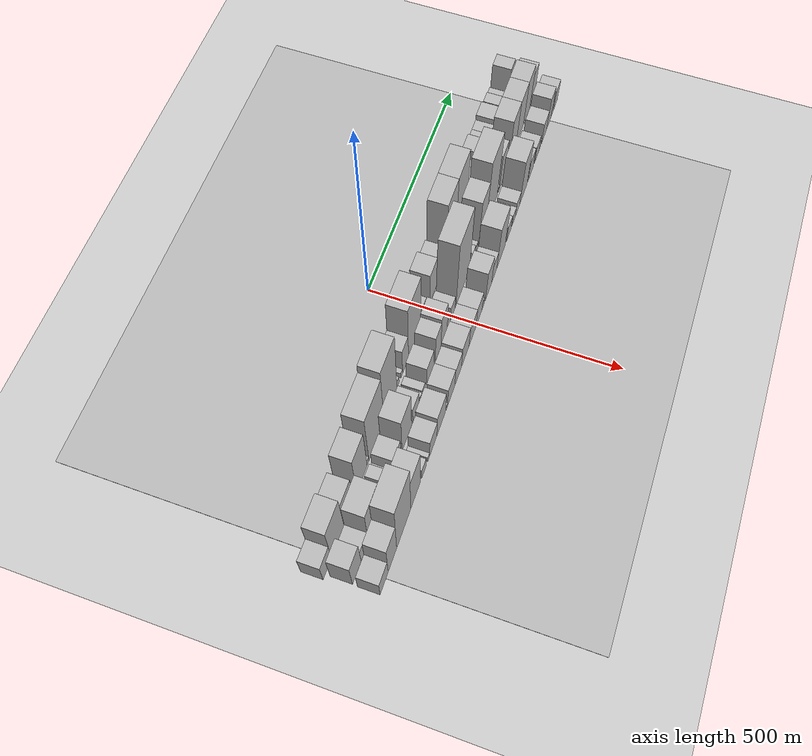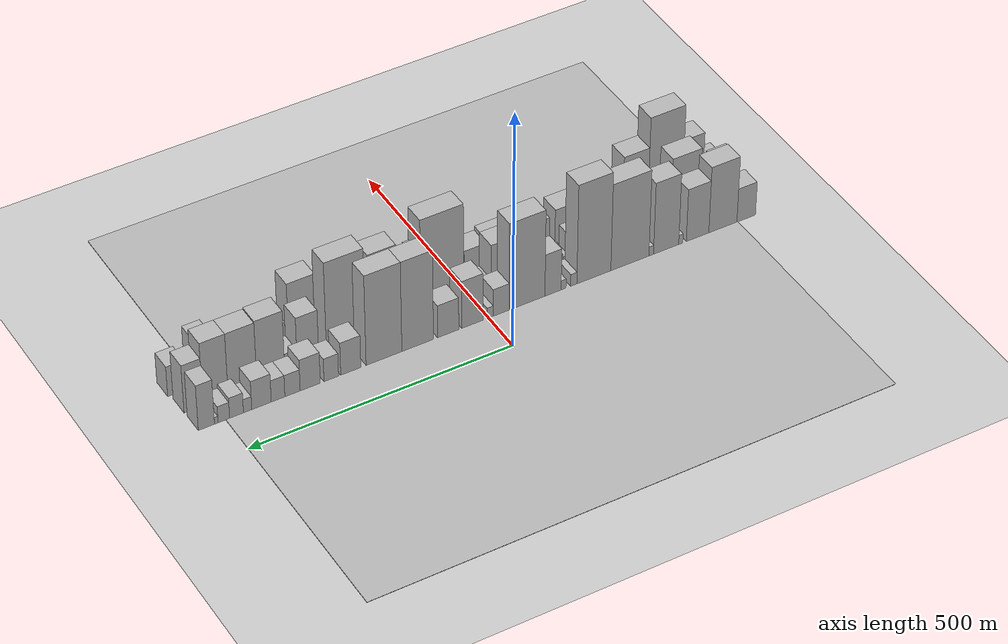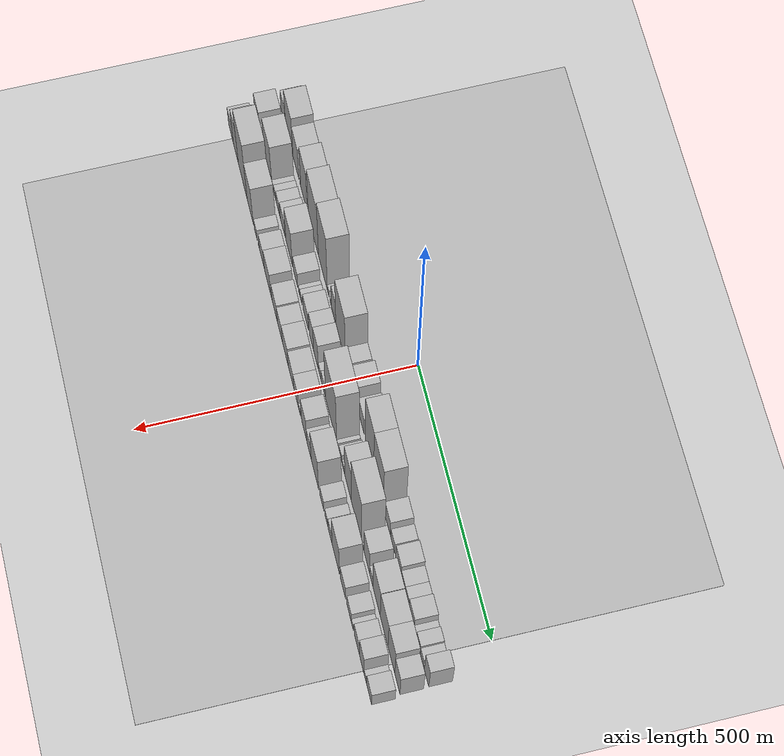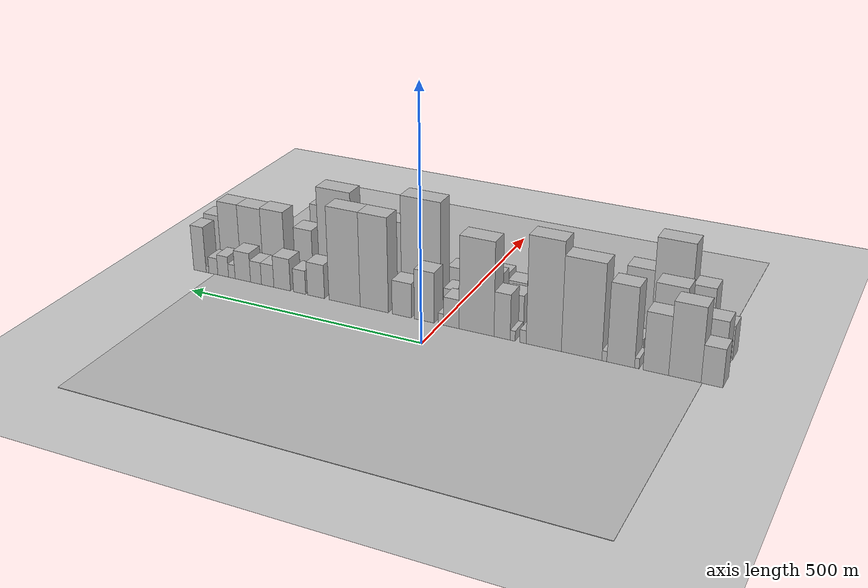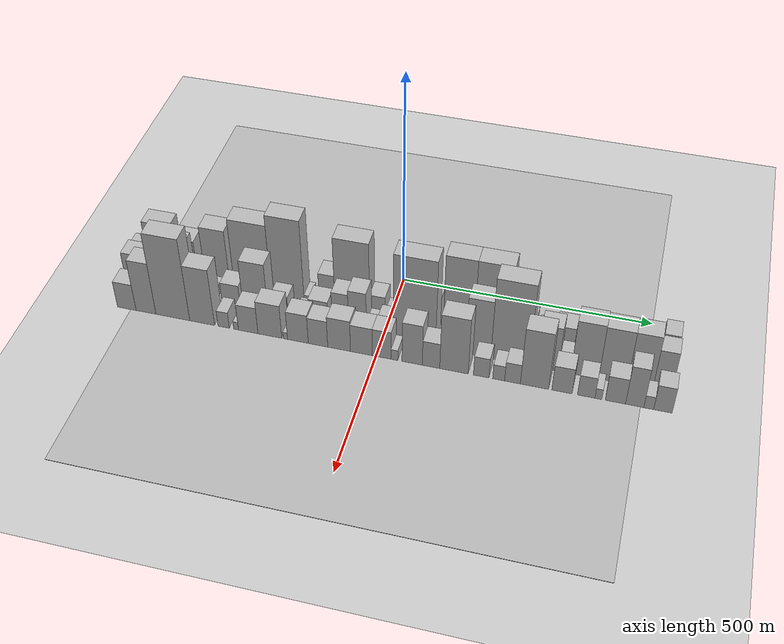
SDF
<?xml version="1.0" encoding="utf-8"?>

<sdf version="1.6">

   <world name="default">

      <gui fullscreen="0">

         <camera name="user_camera">

            <pose>-15 0 4.57585 0 0 0</pose>

            <view_controller>orbit</view_controller>

         </camera>

      </gui>

      <scene>

         <sky>

           <clouds>

             <speed>12</speed>

           </clouds>

         </sky>

         <ambient>0.4 0.4 0.4 1</ambient>

         <background>0.7 0.7 0.7 1</background>

         <shadows>1</shadows>

      </scene>

      <gravity>0 0 -9.8066</gravity>

      <magnetic_field>6e-06 2.3e-05 -4.2e-05</magnetic_field>

      <physics default="0" name="default_physics" type="ode">

         <ode>

            <solver>

               <type>quick</type>

               <iters>10</iters>

               <sor>1.0</sor>

               <use_dynamic_moi_rescaling>0</use_dynamic_moi_rescaling>

            </solver>

            <constraints>

               <cfm>0</cfm>

               <erp>0.2</erp>

               <contact_max_correcting_vel>100</contact_max_correcting_vel>

               <contact_surface_layer>0.001</contact_surface_layer>

            </constraints>

         </ode>

         <max_step_size>0.004</max_step_size>

         <real_time_factor>1</real_time_factor>

         <real_time_update_rate>250</real_time_update_rate>

      </physics>

      <light name="sun" type="directional">

         <cast_shadows>1</cast_shadows>

         <pose>0 0 10 0 0 0</pose>

         <diffuse>0.8 0.8 0.8 1</diffuse>

         <specular>0.2 0.2 0.2 1</specular>

         <attenuation>

            <range>1000</range>

            <constant>0.9</constant>

            <linear>0.01</linear>

            <quadratic>0.001</quadratic>

         </attenuation>

         <direction>-0.5 0.1 -0.9</direction>

      </light>

      <include>

         <name>ground_plane_1</name>

         <uri>model://HANNAS_ground_plane</uri>

         <pose>0 0 0  0 0 0</pose>

      </include>

      <include>

         <name>ground_plane_2</name>

         <uri>model://HANNAS_ground_plane</uri>

         <pose>100 0 0  0 0 0</pose>

      </include>

      <model name="building_1">

         <static>1</static>

         <pose frame="">100.0000 -516.7739 0 0.000000 0.000000 0.000000</pose>

         <link name="link">

            <pose frame="">0 0 37.50 0 0 0</pose>

            <collision name="collision">

               <geometry>

                  <box>

                     <size>40.0000 38.4522 75.0000</size>

                  </box>

               </geometry>

               <max_contacts>10</max_contacts>

               <surface>

                  <contact>

                     <ode/>

                  </contact>

                  <bounce/>

                  <friction>

                     <torsional>

                        <ode/>

                     </torsional>

                     <ode/>

                  </friction>

               </surface>

            </collision>

            <visual name="visual">

               <cast_shadows>0</cast_shadows>

               <geometry>

                  <box>

                     <size>40.0000 38.4522 75.0000</size>

                  </box>

               </geometry>

               <material>

                  <script>

                     <uri>model://HANNAS_wall/materials/scripts</uri>

                     <uri>model://HANNAS_wall/materials/textures</uri>

                     <name>vrc/HANNAS_wall</name>

                  </script>

               </material>

            </visual>

            <self_collide>0</self_collide>

            <enable_wind>0</enable_wind>

            <kinematic>0</kinematic>

         </link>

      </model>

      <model name="building_2">

         <static>1</static>

         <pose frame="">100.0000 -468.6095 0 0.000000 0.000000 0.000000</pose>

         <link name="link">

            <pose frame="">0 0 73.50 0 0 0</pose>

            <collision name="collision">

               <geometry>

                  <box>

                     <size>40.0000 57.8766 147.0000</size>

                  </box>

               </geometry>

               <max_contacts>10</max_contacts>

               <surface>

                  <contact>

                     <ode/>

                  </contact>

                  <bounce/>

                  <friction>

                     <torsional>

                        <ode/>

                     </torsional>

                     <ode/>

                  </friction>

               </surface>

            </collision>

            <visual name="visual">

               <cast_shadows>0</cast_shadows>

               <geometry>

                  <box>

                     <size>40.0000 57.8766 147.0000</size>

                  </box>

               </geometry>

               <material>

                  <script>

                     <uri>model://HANNAS_wall/materials/scripts</uri>

                     <uri>model://HANNAS_wall/materials/textures</uri>

                     <name>vrc/HANNAS_wall</name>

                  </script>

               </material>

            </visual>

            <self_collide>0</self_collide>

            <enable_wind>0</enable_wind>

            <kinematic>0</kinematic>

         </link>

      </model>

      <model name="building_3">

         <static>1</static>

         <pose frame="">100.0000 -416.5779 0 0.000000 0.000000 0.000000</pose>

         <link name="link">

            <pose frame="">0 0 58.50 0 0 0</pose>

            <collision name="collision">

               <geometry>

                  <box>

                     <size>40.0000 46.1865 117.0000</size>

                  </box>

               </geometry>

               <max_contacts>10</max_contacts>

               <surface>

                  <contact>

                     <ode/>

                  </contact>

                  <bounce/>

                  <friction>

                     <torsional>

                        <ode/>

                     </torsional>

                     <ode/>

                  </friction>

               </surface>

            </collision>

            <visual name="visual">

               <cast_shadows>0</cast_shadows>

               <geometry>

                  <box>

                     <size>40.0000 46.1865 117.0000</size>

                  </box>

               </geometry>

               <material>

                  <script>

                     <uri>model://HANNAS_wall/materials/scripts</uri>

                     <uri>model://HANNAS_wall/materials/textures</uri>

                     <name>vrc/HANNAS_wall</name>

                  </script>

               </material>

            </visual>

            <self_collide>0</self_collide>

            <enable_wind>0</enable_wind>

            <kinematic>0</kinematic>

         </link>

      </model>

      <model name="building_4">

         <static>1</static>

         <pose frame="">100.0000 -382.2491 0 0.000000 0.000000 0.000000</pose>

         <link name="link">

            <pose frame="">0 0 10.50 0 0 0</pose>

            <collision name="collision">

               <geometry>

                  <box>

                     <size>40.0000 8.4712 21.0000</size>

                  </box>

               </geometry>

               <max_contacts>10</max_contacts>

               <surface>

                  <contact>

                     <ode/>

                  </contact>

                  <bounce/>

                  <friction>

                     <torsional>

                        <ode/>

                     </torsional>

                     <ode/>

                  </friction>

               </surface>

            </collision>

            <visual name="visual">

               <cast_shadows>0</cast_shadows>

               <geometry>

                  <box>

                     <size>40.0000 8.4712 21.0000</size>

                  </box>

               </geometry>

               <material>

                  <script>

                     <uri>model://HANNAS_wall/materials/scripts</uri>

                     <uri>model://HANNAS_wall/materials/textures</uri>

                     <name>vrc/HANNAS_wall</name>

                  </script>

               </material>

            </visual>

            <self_collide>0</self_collide>

            <enable_wind>0</enable_wind>

            <kinematic>0</kinematic>

         </link>

      </model>

      <model name="building_5">

         <static>1</static>

         <pose frame="">100.0000 -352.4027 0 0.000000 0.000000 0.000000</pose>

         <link name="link">

            <pose frame="">0 0 79.50 0 0 0</pose>

            <collision name="collision">

               <geometry>

                  <box>

                     <size>40.0000 51.2216 159.0000</size>

                  </box>

               </geometry>

               <max_contacts>10</max_contacts>

               <surface>

                  <contact>

                     <ode/>

                  </contact>

                  <bounce/>

                  <friction>

                     <torsional>

                        <ode/>

                     </torsional>

                     <ode/>

                  </friction>

               </surface>

            </collision>

            <visual name="visual">

               <cast_shadows>0</cast_shadows>

               <geometry>

                  <box>

                     <size>40.0000 51.2216 159.0000</size>

                  </box>

               </geometry>

               <material>

                  <script>

                     <uri>model://HANNAS_wall/materials/scripts</uri>

                     <uri>model://HANNAS_wall/materials/textures</uri>

                     <name>vrc/HANNAS_wall</name>

                  </script>

               </material>

            </visual>

            <self_collide>0</self_collide>

            <enable_wind>0</enable_wind>

            <kinematic>0</kinematic>

         </link>

      </model>

      <model name="building_6">

         <static>1</static>

         <pose frame="">100.0000 -322.1300 0 0.000000 0.000000 0.000000</pose>

         <link name="link">

            <pose frame="">0 0 10.50 0 0 0</pose>

            <collision name="collision">

               <geometry>

                  <box>

                     <size>40.0000 9.3240 21.0000</size>

                  </box>

               </geometry>

               <max_contacts>10</max_contacts>

               <surface>

                  <contact>

                     <ode/>

                  </contact>

                  <bounce/>

                  <friction>

                     <torsional>

                        <ode/>

                     </torsional>

                     <ode/>

                  </friction>

               </surface>

            </collision>

            <visual name="visual">

               <cast_shadows>0</cast_shadows>

               <geometry>

                  <box>

                     <size>40.0000 9.3240 21.0000</size>

                  </box>

               </geometry>

               <material>

                  <script>

                     <uri>model://HANNAS_wall/materials/scripts</uri>

                     <uri>model://HANNAS_wall/materials/textures</uri>

                     <name>vrc/HANNAS_wall</name>

                  </script>

               </material>

            </visual>

            <self_collide>0</self_collide>

            <enable_wind>0</enable_wind>

            <kinematic>0</kinematic>

         </link>

      </model>

      <model name="building_7">

         <static>1</static>

         <pose frame="">100.0000 -279.0681 0 0.000000 0.000000 0.000000</pose>

         <link name="link">

            <pose frame="">0 0 96.00 0 0 0</pose>

            <collision name="collision">

               <geometry>

                  <box>

                     <size>40.0000 76.7997 192.0000</size>

                  </box>

               </geometry>

               <max_contacts>10</max_contacts>

               <surface>

                  <contact>

                     <ode/>

                  </contact>

                  <bounce/>

                  <friction>

                     <torsional>

                        <ode/>

                     </torsional>

                     <ode/>

                  </friction>

               </surface>

            </collision>

            <visual name="visual">

               <cast_shadows>0</cast_shadows>

               <geometry>

                  <box>

                     <size>40.0000 76.7997 192.0000</size>

                  </box>

               </geometry>

               <material>

                  <script>

                     <uri>model://HANNAS_wall/materials/scripts</uri>

                     <uri>model://HANNAS_wall/materials/textures</uri>

                     <name>vrc/HANNAS_wall</name>

                  </script>

               </material>

            </visual>

            <self_collide>0</self_collide>

            <enable_wind>0</enable_wind>

            <kinematic>0</kinematic>

         </link>

      </model>

      <model name="building_8">

         <static>1</static>

         <pose frame="">100.0000 -206.6568 0 0.000000 0.000000 0.000000</pose>

         <link name="link">

            <pose frame="">0 0 109.50 0 0 0</pose>

            <collision name="collision">

               <geometry>

                  <box>

                     <size>40.0000 68.0230 219.0000</size>

                  </box>

               </geometry>

               <max_contacts>10</max_contacts>

               <surface>

                  <contact>

                     <ode/>

                  </contact>

                  <bounce/>

                  <friction>

                     <torsional>

                        <ode/>

                     </torsional>

                     <ode/>

                  </friction>

               </surface>

            </collision>

            <visual name="visual">

               <cast_shadows>0</cast_shadows>

               <geometry>

                  <box>

                     <size>40.0000 68.0230 219.0000</size>

                  </box>

               </geometry>

               <material>

                  <script>

                     <uri>model://HANNAS_wall/materials/scripts</uri>

                     <uri>model://HANNAS_wall/materials/textures</uri>

                     <name>vrc/HANNAS_wall</name>

                  </script>

               </material>

            </visual>

            <self_collide>0</self_collide>

            <enable_wind>0</enable_wind>

            <kinematic>0</kinematic>

         </link>

      </model>

      <model name="building_9">

         <static>1</static>

         <pose frame="">100.0000 -166.4375 0 0.000000 0.000000 0.000000</pose>

         <link name="link">

            <pose frame="">0 0 13.50 0 0 0</pose>

            <collision name="collision">

               <geometry>

                  <box>

                     <size>40.0000 12.4156 27.0000</size>

                  </box>

               </geometry>

               <max_contacts>10</max_contacts>

               <surface>

                  <contact>

                     <ode/>

                  </contact>

                  <bounce/>

                  <friction>

                     <torsional>

                        <ode/>

                     </torsional>

                     <ode/>

                  </friction>

               </surface>

            </collision>

            <visual name="visual">

               <cast_shadows>0</cast_shadows>

               <geometry>

                  <box>

                     <size>40.0000 12.4156 27.0000</size>

                  </box>

               </geometry>

               <material>

                  <script>

                     <uri>model://HANNAS_wall/materials/scripts</uri>

                     <uri>model://HANNAS_wall/materials/textures</uri>

                     <name>vrc/HANNAS_wall</name>

                  </script>

               </material>

            </visual>

            <self_collide>0</self_collide>

            <enable_wind>0</enable_wind>

            <kinematic>0</kinematic>

         </link>

      </model>

      <model name="building_10">

         <static>1</static>

         <pose frame="">100.0000 -146.2951 0 0.000000 0.000000 0.000000</pose>

         <link name="link">

            <pose frame="">0 0 10.50 0 0 0</pose>

            <collision name="collision">

               <geometry>

                  <box>

                     <size>40.0000 9.8693 21.0000</size>

                  </box>

               </geometry>

               <max_contacts>10</max_contacts>

               <surface>

                  <contact>

                     <ode/>

                  </contact>

                  <bounce/>

                  <friction>

                     <torsional>

                        <ode/>

                     </torsional>

                     <ode/>

                  </friction>

               </surface>

            </collision>

            <visual name="visual">

               <cast_shadows>0</cast_shadows>

               <geometry>

                  <box>

                     <size>40.0000 9.8693 21.0000</size>

                  </box>

               </geometry>

               <material>

                  <script>

                     <uri>model://HANNAS_wall/materials/scripts</uri>

                     <uri>model://HANNAS_wall/materials/textures</uri>

                     <name>vrc/HANNAS_wall</name>

                  </script>

               </material>

            </visual>

            <self_collide>0</self_collide>

            <enable_wind>0</enable_wind>

            <kinematic>0</kinematic>

         </link>

      </model>

      <model name="building_11">

         <static>1</static>

         <pose frame="">100.0000 -125.3299 0 0.000000 0.000000 0.000000</pose>

         <link name="link">

            <pose frame="">0 0 46.50 0 0 0</pose>

            <collision name="collision">

               <geometry>

                  <box>

                     <size>40.0000 32.0611 93.0000</size>

                  </box>

               </geometry>

               <max_contacts>10</max_contacts>

               <surface>

                  <contact>

                     <ode/>

                  </contact>

                  <bounce/>

                  <friction>

                     <torsional>

                        <ode/>

                     </torsional>

                     <ode/>

                  </friction>

               </surface>

            </collision>

            <visual name="visual">

               <cast_shadows>0</cast_shadows>

               <geometry>

                  <box>

                     <size>40.0000 32.0611 93.0000</size>

                  </box>

               </geometry>

               <material>

                  <script>

                     <uri>model://HANNAS_wall/materials/scripts</uri>

                     <uri>model://HANNAS_wall/materials/textures</uri>

                     <name>vrc/HANNAS_wall</name>

                  </script>

               </material>

            </visual>

            <self_collide>0</self_collide>

            <enable_wind>0</enable_wind>

            <kinematic>0</kinematic>

         </link>

      </model>

      <model name="building_12">

         <static>1</static>

         <pose frame="">100.0000 -74.0679 0 0.000000 0.000000 0.000000</pose>

         <link name="link">

            <pose frame="">0 0 96.00 0 0 0</pose>

            <collision name="collision">

               <geometry>

                  <box>

                     <size>40.0000 70.4630 192.0000</size>

                  </box>

               </geometry>

               <max_contacts>10</max_contacts>

               <surface>

                  <contact>

                     <ode/>

                  </contact>

                  <bounce/>

                  <friction>

                     <torsional>

                        <ode/>

                     </torsional>

                     <ode/>

                  </friction>

               </surface>

            </collision>

            <visual name="visual">

               <cast_shadows>0</cast_shadows>

               <geometry>

                  <box>

                     <size>40.0000 70.4630 192.0000</size>

                  </box>

               </geometry>

               <material>

                  <script>

                     <uri>model://HANNAS_wall/materials/scripts</uri>

                     <uri>model://HANNAS_wall/materials/textures</uri>

                     <name>vrc/HANNAS_wall</name>

                  </script>

               </material>

            </visual>

            <self_collide>0</self_collide>

            <enable_wind>0</enable_wind>

            <kinematic>0</kinematic>

         </link>

      </model>

      <model name="building_13">

         <static>1</static>

         <pose frame="">100.0000 -23.1314 0 0.000000 0.000000 0.000000</pose>

         <link name="link">

            <pose frame="">0 0 30.00 0 0 0</pose>

            <collision name="collision">

               <geometry>

                  <box>

                     <size>40.0000 31.4100 60.0000</size>

                  </box>

               </geometry>

               <max_contacts>10</max_contacts>

               <surface>

                  <contact>

                     <ode/>

                  </contact>

                  <bounce/>

                  <friction>

                     <torsional>

                        <ode/>

                     </torsional>

                     <ode/>

                  </friction>

               </surface>

            </collision>

            <visual name="visual">

               <cast_shadows>0</cast_shadows>

               <geometry>

                  <box>

                     <size>40.0000 31.4100 60.0000</size>

                  </box>

               </geometry>

               <material>

                  <script>

                     <uri>model://HANNAS_wall/materials/scripts</uri>

                     <uri>model://HANNAS_wall/materials/textures</uri>

                     <name>vrc/HANNAS_wall</name>

                  </script>

               </material>

            </visual>

            <self_collide>0</self_collide>

            <enable_wind>0</enable_wind>

            <kinematic>0</kinematic>

         </link>

      </model>

      <model name="building_14">

         <static>1</static>

         <pose frame="">100.0000 -1.5703 0 0.000000 0.000000 0.000000</pose>

         <link name="link">

            <pose frame="">0 0 12.00 0 0 0</pose>

            <collision name="collision">

               <geometry>

                  <box>

                     <size>40.0000 11.7123 24.0000</size>

                  </box>

               </geometry>

               <max_contacts>10</max_contacts>

               <surface>

                  <contact>

                     <ode/>

                  </contact>

                  <bounce/>

                  <friction>

                     <torsional>

                        <ode/>

                     </torsional>

                     <ode/>

                  </friction>

               </surface>

            </collision>

            <visual name="visual">

               <cast_shadows>0</cast_shadows>

               <geometry>

                  <box>

                     <size>40.0000 11.7123 24.0000</size>

                  </box>

               </geometry>

               <material>

                  <script>

                     <uri>model://HANNAS_wall/materials/scripts</uri>

                     <uri>model://HANNAS_wall/materials/textures</uri>

                     <name>vrc/HANNAS_wall</name>

                  </script>

               </material>

            </visual>

            <self_collide>0</self_collide>

            <enable_wind>0</enable_wind>

            <kinematic>0</kinematic>

         </link>

      </model>

      <model name="building_15">

         <static>1</static>

         <pose frame="">100.0000 32.9427 0 0.000000 0.000000 0.000000</pose>

         <link name="link">

            <pose frame="">0 0 52.50 0 0 0</pose>

            <collision name="collision">

               <geometry>

                  <box>

                     <size>40.0000 41.3135 105.0000</size>

                  </box>

               </geometry>

               <max_contacts>10</max_contacts>

               <surface>

                  <contact>

                     <ode/>

                  </contact>

                  <bounce/>

                  <friction>

                     <torsional>

                        <ode/>

                     </torsional>

                     <ode/>

                  </friction>

               </surface>

            </collision>

            <visual name="visual">

               <cast_shadows>0</cast_shadows>

               <geometry>

                  <box>

                     <size>40.0000 41.3135 105.0000</size>

                  </box>

               </geometry>

               <material>

                  <script>

                     <uri>model://HANNAS_wall/materials/scripts</uri>

                     <uri>model://HANNAS_wall/materials/textures</uri>

                     <name>vrc/HANNAS_wall</name>

                  </script>

               </material>

            </visual>

            <self_collide>0</self_collide>

            <enable_wind>0</enable_wind>

            <kinematic>0</kinematic>

         </link>

      </model>

      <model name="building_16">

         <static>1</static>

         <pose frame="">100.0000 80.0405 0 0.000000 0.000000 0.000000</pose>

         <link name="link">

            <pose frame="">0 0 36.00 0 0 0</pose>

            <collision name="collision">

               <geometry>

                  <box>

                     <size>40.0000 40.8822 72.0000</size>

                  </box>

               </geometry>

               <max_contacts>10</max_contacts>

               <surface>

                  <contact>

                     <ode/>

                  </contact>

                  <bounce/>

                  <friction>

                     <torsional>

                        <ode/>

                     </torsional>

                     <ode/>

                  </friction>

               </surface>

            </collision>

            <visual name="visual">

               <cast_shadows>0</cast_shadows>

               <geometry>

                  <box>

                     <size>40.0000 40.8822 72.0000</size>

                  </box>

               </geometry>

               <material>

                  <script>

                     <uri>model://HANNAS_wall/materials/scripts</uri>

                     <uri>model://HANNAS_wall/materials/textures</uri>

                     <name>vrc/HANNAS_wall</name>

                  </script>

               </material>

            </visual>

            <self_collide>0</self_collide>

            <enable_wind>0</enable_wind>

            <kinematic>0</kinematic>

         </link>

      </model>

      <model name="building_17">

         <static>1</static>

         <pose frame="">100.0000 138.8409 0 0.000000 0.000000 0.000000</pose>

         <link name="link">

            <pose frame="">0 0 99.00 0 0 0</pose>

            <collision name="collision">

               <geometry>

                  <box>

                     <size>40.0000 60.7184 198.0000</size>

                  </box>

               </geometry>

               <max_contacts>10</max_contacts>

               <surface>

                  <contact>

                     <ode/>

                  </contact>

                  <bounce/>

                  <friction>

                     <torsional>

                        <ode/>

                     </torsional>

                     <ode/>

                  </friction>

               </surface>

            </collision>

            <visual name="visual">

               <cast_shadows>0</cast_shadows>

               <geometry>

                  <box>

                     <size>40.0000 60.7184 198.0000</size>

                  </box>

               </geometry>

               <material>

                  <script>

                     <uri>model://HANNAS_wall/materials/scripts</uri>

                     <uri>model://HANNAS_wall/materials/textures</uri>

                     <name>vrc/HANNAS_wall</name>

                  </script>

               </material>

            </visual>

            <self_collide>0</self_collide>

            <enable_wind>0</enable_wind>

            <kinematic>0</kinematic>

         </link>

      </model>

      <model name="building_18">

         <static>1</static>

         <pose frame="">100.0000 203.3667 0 0.000000 0.000000 0.000000</pose>

         <link name="link">

            <pose frame="">0 0 99.00 0 0 0</pose>

            <collision name="collision">

               <geometry>

                  <box>

                     <size>40.0000 68.3333 198.0000</size>

                  </box>

               </geometry>

               <max_contacts>10</max_contacts>

               <surface>

                  <contact>

                     <ode/>

                  </contact>

                  <bounce/>

                  <friction>

                     <torsional>

                        <ode/>

                     </torsional>

                     <ode/>

                  </friction>

               </surface>

            </collision>

            <visual name="visual">

               <cast_shadows>0</cast_shadows>

               <geometry>

                  <box>

                     <size>40.0000 68.3333 198.0000</size>

                  </box>

               </geometry>

               <material>

                  <script>

                     <uri>model://HANNAS_wall/materials/scripts</uri>

                     <uri>model://HANNAS_wall/materials/textures</uri>

                     <name>vrc/HANNAS_wall</name>

                  </script>

               </material>

            </visual>

            <self_collide>0</self_collide>

            <enable_wind>0</enable_wind>

            <kinematic>0</kinematic>

         </link>

      </model>

      <model name="building_19">

         <static>1</static>

         <pose frame="">100.0000 266.5942 0 0.000000 0.000000 0.000000</pose>

         <link name="link">

            <pose frame="">0 0 36.00 0 0 0</pose>

            <collision name="collision">

               <geometry>

                  <box>

                     <size>40.0000 38.1216 72.0000</size>

                  </box>

               </geometry>

               <max_contacts>10</max_contacts>

               <surface>

                  <contact>

                     <ode/>

                  </contact>

                  <bounce/>

                  <friction>

                     <torsional>

                        <ode/>

                     </torsional>

                     <ode/>

                  </friction>

               </surface>

            </collision>

            <visual name="visual">

               <cast_shadows>0</cast_shadows>

               <geometry>

                  <box>

                     <size>40.0000 38.1216 72.0000</size>

                  </box>

               </geometry>

               <material>

                  <script>

                     <uri>model://HANNAS_wall/materials/scripts</uri>

                     <uri>model://HANNAS_wall/materials/textures</uri>

                     <name>vrc/HANNAS_wall</name>

                  </script>

               </material>

            </visual>

            <self_collide>0</self_collide>

            <enable_wind>0</enable_wind>

            <kinematic>0</kinematic>

         </link>

      </model>

      <model name="building_20">

         <static>1</static>

         <pose frame="">100.0000 303.4126 0 0.000000 0.000000 0.000000</pose>

         <link name="link">

            <pose frame="">0 0 25.50 0 0 0</pose>

            <collision name="collision">

               <geometry>

                  <box>

                     <size>40.0000 27.5153 51.0000</size>

                  </box>

               </geometry>

               <max_contacts>10</max_contacts>

               <surface>

                  <contact>

                     <ode/>

                  </contact>

                  <bounce/>

                  <friction>

                     <torsional>

                        <ode/>

                     </torsional>

                     <ode/>

                  </friction>

               </surface>

            </collision>

            <visual name="visual">

               <cast_shadows>0</cast_shadows>

               <geometry>

                  <box>

                     <size>40.0000 27.5153 51.0000</size>

                  </box>

               </geometry>

               <material>

                  <script>

                     <uri>model://HANNAS_wall/materials/scripts</uri>

                     <uri>model://HANNAS_wall/materials/textures</uri>

                     <name>vrc/HANNAS_wall</name>

                  </script>

               </material>

            </visual>

            <self_collide>0</self_collide>

            <enable_wind>0</enable_wind>

            <kinematic>0</kinematic>

         </link>

      </model>

      <model name="building_21">

         <static>1</static>

         <pose frame="">100.0000 343.0407 0 0.000000 0.000000 0.000000</pose>

         <link name="link">

            <pose frame="">0 0 34.50 0 0 0</pose>

            <collision name="collision">

               <geometry>

                  <box>

                     <size>40.0000 37.7409 69.0000</size>

                  </box>

               </geometry>

               <max_contacts>10</max_contacts>

               <surface>

                  <contact>

                     <ode/>

                  </contact>

                  <bounce/>

                  <friction>

                     <torsional>

                        <ode/>

                     </torsional>

                     <ode/>

                  </friction>

               </surface>

            </collision>

            <visual name="visual">

               <cast_shadows>0</cast_shadows>

               <geometry>

                  <box>

                     <size>40.0000 37.7409 69.0000</size>

                  </box>

               </geometry>

               <material>

                  <script>

                     <uri>model://HANNAS_wall/materials/scripts</uri>

                     <uri>model://HANNAS_wall/materials/textures</uri>

                     <name>vrc/HANNAS_wall</name>

                  </script>

               </material>

            </visual>

            <self_collide>0</self_collide>

            <enable_wind>0</enable_wind>

            <kinematic>0</kinematic>

         </link>

      </model>

      <model name="building_22">

         <static>1</static>

         <pose frame="">100.0000 376.2095 0 0.000000 0.000000 0.000000</pose>

         <link name="link">

            <pose frame="">0 0 24.00 0 0 0</pose>

            <collision name="collision">

               <geometry>

                  <box>

                     <size>40.0000 28.5967 48.0000</size>

                  </box>

               </geometry>

               <max_contacts>10</max_contacts>

               <surface>

                  <contact>

                     <ode/>

                  </contact>

                  <bounce/>

                  <friction>

                     <torsional>

                        <ode/>

                     </torsional>

                     <ode/>

                  </friction>

               </surface>

            </collision>

            <visual name="visual">

               <cast_shadows>0</cast_shadows>

               <geometry>

                  <box>

                     <size>40.0000 28.5967 48.0000</size>

                  </box>

               </geometry>

               <material>

                  <script>

                     <uri>model://HANNAS_wall/materials/scripts</uri>

                     <uri>model://HANNAS_wall/materials/textures</uri>

                     <name>vrc/HANNAS_wall</name>

                  </script>

               </material>

            </visual>

            <self_collide>0</self_collide>

            <enable_wind>0</enable_wind>

            <kinematic>0</kinematic>

         </link>

      </model>

      <model name="building_23">

         <static>1</static>

         <pose frame="">100.0000 403.1904 0 0.000000 0.000000 0.000000</pose>

         <link name="link">

            <pose frame="">0 0 24.00 0 0 0</pose>

            <collision name="collision">

               <geometry>

                  <box>

                     <size>40.0000 25.3651 48.0000</size>

                  </box>

               </geometry>

               <max_contacts>10</max_contacts>

               <surface>

                  <contact>

                     <ode/>

                  </contact>

                  <bounce/>

                  <friction>

                     <torsional>

                        <ode/>

                     </torsional>

                     <ode/>

                  </friction>

               </surface>

            </collision>

            <visual name="visual">

               <cast_shadows>0</cast_shadows>

               <geometry>

                  <box>

                     <size>40.0000 25.3651 48.0000</size>

                  </box>

               </geometry>

               <material>

                  <script>

                     <uri>model://HANNAS_wall/materials/scripts</uri>

                     <uri>model://HANNAS_wall/materials/textures</uri>

                     <name>vrc/HANNAS_wall</name>

                  </script>

               </material>

            </visual>

            <self_collide>0</self_collide>

            <enable_wind>0</enable_wind>

            <kinematic>0</kinematic>

         </link>

      </model>

      <model name="building_24">

         <static>1</static>

         <pose frame="">100.0000 433.9990 0 0.000000 0.000000 0.000000</pose>

         <link name="link">

            <pose frame="">0 0 31.50 0 0 0</pose>

            <collision name="collision">

               <geometry>

                  <box>

                     <size>40.0000 36.2522 63.0000</size>

                  </box>

               </geometry>

               <max_contacts>10</max_contacts>

               <surface>

                  <contact>

                     <ode/>

                  </contact>

                  <bounce/>

                  <friction>

                     <torsional>

                        <ode/>

                     </torsional>

                     <ode/>

                  </friction>

               </surface>

            </collision>

            <visual name="visual">

               <cast_shadows>0</cast_shadows>

               <geometry>

                  <box>

                     <size>40.0000 36.2522 63.0000</size>

                  </box>

               </geometry>

               <material>

                  <script>

                     <uri>model://HANNAS_wall/materials/scripts</uri>

                     <uri>model://HANNAS_wall/materials/textures</uri>

                     <name>vrc/HANNAS_wall</name>

                  </script>

               </material>

            </visual>

            <self_collide>0</self_collide>

            <enable_wind>0</enable_wind>

            <kinematic>0</kinematic>

         </link>

      </model>

      <model name="building_25">

         <static>1</static>

         <pose frame="">100.0000 459.8254 0 0.000000 0.000000 0.000000</pose>

         <link name="link">

            <pose frame="">0 0 15.00 0 0 0</pose>

            <collision name="collision">

               <geometry>

                  <box>

                     <size>40.0000 15.4006 30.0000</size>

                  </box>

               </geometry>

               <max_contacts>10</max_contacts>

               <surface>

                  <contact>

                     <ode/>

                  </contact>

                  <bounce/>

                  <friction>

                     <torsional>

                        <ode/>

                     </torsional>

                     <ode/>

                  </friction>

               </surface>

            </collision>

            <visual name="visual">

               <cast_shadows>0</cast_shadows>

               <geometry>

                  <box>

                     <size>40.0000 15.4006 30.0000</size>

                  </box>

               </geometry>

               <material>

                  <script>

                     <uri>model://HANNAS_wall/materials/scripts</uri>

                     <uri>model://HANNAS_wall/materials/textures</uri>

                     <name>vrc/HANNAS_wall</name>

                  </script>

               </material>

            </visual>

            <self_collide>0</self_collide>

            <enable_wind>0</enable_wind>

            <kinematic>0</kinematic>

         </link>

      </model>

      <model name="building_26">

         <static>1</static>

         <pose frame="">100.0000 480.3086 0 0.000000 0.000000 0.000000</pose>

         <link name="link">

            <pose frame="">0 0 22.50 0 0 0</pose>

            <collision name="collision">

               <geometry>

                  <box>

                     <size>40.0000 25.5657 45.0000</size>

                  </box>

               </geometry>

               <max_contacts>10</max_contacts>

               <surface>

                  <contact>

                     <ode/>

                  </contact>

                  <bounce/>

                  <friction>

                     <torsional>

                        <ode/>

                     </torsional>

                     <ode/>

                  </friction>

               </surface>

            </collision>

            <visual name="visual">

               <cast_shadows>0</cast_shadows>

               <geometry>

                  <box>

                     <size>40.0000 25.5657 45.0000</size>

                  </box>

               </geometry>

               <material>

                  <script>

                     <uri>model://HANNAS_wall/materials/scripts</uri>

                     <uri>model://HANNAS_wall/materials/textures</uri>

                     <name>vrc/HANNAS_wall</name>

                  </script>

               </material>

            </visual>

            <self_collide>0</self_collide>

            <enable_wind>0</enable_wind>

            <kinematic>0</kinematic>

         </link>

      </model>

      <model name="building_27">

         <static>1</static>

         <pose frame="">100.0000 503.7070 0 0.000000 0.000000 0.000000</pose>

         <link name="link">

            <pose frame="">0 0 18.00 0 0 0</pose>

            <collision name="collision">

               <geometry>

                  <box>

                     <size>40.0000 21.2311 36.0000</size>

                  </box>

               </geometry>

               <max_contacts>10</max_contacts>

               <surface>

                  <contact>

                     <ode/>

                  </contact>

                  <bounce/>

                  <friction>

                     <torsional>

                        <ode/>

                     </torsional>

                     <ode/>

                  </friction>

               </surface>

            </collision>

            <visual name="visual">

               <cast_shadows>0</cast_shadows>

               <geometry>

                  <box>

                     <size>40.0000 21.2311 36.0000</size>

                  </box>

               </geometry>

               <material>

                  <script>

                     <uri>model://HANNAS_wall/materials/scripts</uri>

                     <uri>model://HANNAS_wall/materials/textures</uri>

                     <name>vrc/HANNAS_wall</name>

                  </script>

               </material>

            </visual>

            <self_collide>0</self_collide>

            <enable_wind>0</enable_wind>

            <kinematic>0</kinematic>

         </link>

      </model>

      <model name="building_28">

         <static>1</static>

         <pose frame="">100.0000 517.6253 0 0.000000 0.000000 0.000000</pose>

         <link name="link">

            <pose frame="">0 0 7.50 0 0 0</pose>

            <collision name="collision">

               <geometry>

                  <box>

                     <size>40.0000 6.6057 15.0000</size>

                  </box>

               </geometry>

               <max_contacts>10</max_contacts>

               <surface>

                  <contact>

                     <ode/>

                  </contact>

                  <bounce/>

                  <friction>

                     <torsional>

                        <ode/>

                     </torsional>

                     <ode/>

                  </friction>

               </surface>

            </collision>

            <visual name="visual">

               <cast_shadows>0</cast_shadows>

               <geometry>

                  <box>

                     <size>40.0000 6.6057 15.0000</size>

                  </box>

               </geometry>

               <material>

                  <script>

                     <uri>model://HANNAS_wall/materials/scripts</uri>

                     <uri>model://HANNAS_wall/materials/textures</uri>

                     <name>vrc/HANNAS_wall</name>

                  </script>

               </material>

            </visual>

            <self_collide>0</self_collide>

            <enable_wind>0</enable_wind>

            <kinematic>0</kinematic>

         </link>

      </model>

      <model name="building_29">

         <static>1</static>

         <pose frame="">100.0000 535.8227 0 0.000000 0.000000 0.000000</pose>

         <link name="link">

            <pose frame="">0 0 49.50 0 0 0</pose>

            <collision name="collision">

               <geometry>

                  <box>

                     <size>40.0000 29.7891 99.0000</size>

                  </box>

               </geometry>

               <max_contacts>10</max_contacts>

               <surface>

                  <contact>

                     <ode/>

                  </contact>

                  <bounce/>

                  <friction>

                     <torsional>

                        <ode/>

                     </torsional>

                     <ode/>

                  </friction>

               </surface>

            </collision>

            <visual name="visual">

               <cast_shadows>0</cast_shadows>

               <geometry>

                  <box>

                     <size>40.0000 29.7891 99.0000</size>

                  </box>

               </geometry>

               <material>

                  <script>

                     <uri>model://HANNAS_wall/materials/scripts</uri>

                     <uri>model://HANNAS_wall/materials/textures</uri>

                     <name>vrc/HANNAS_wall</name>

                  </script>

               </material>

            </visual>

            <self_collide>0</self_collide>

            <enable_wind>0</enable_wind>

            <kinematic>0</kinematic>

         </link>

      </model>

      <model name="building_30">

         <static>1</static>

         <pose frame="">149.0000 -506.9247 0 0.000000 0.000000 0.000000</pose>

         <link name="link">

            <pose frame="">0 0 51.00 0 0 0</pose>

            <collision name="collision">

               <geometry>

                  <box>

                     <size>40.0000 40.1506 102.0000</size>

                  </box>

               </geometry>

               <max_contacts>10</max_contacts>

               <surface>

                  <contact>

                     <ode/>

                  </contact>

                  <bounce/>

                  <friction>

                     <torsional>

                        <ode/>

                     </torsional>

                     <ode/>

                  </friction>

               </surface>

            </collision>

            <visual name="visual">

               <cast_shadows>0</cast_shadows>

               <geometry>

                  <box>

                     <size>40.0000 40.1506 102.0000</size>

                  </box>

               </geometry>

               <material>

                  <script>

                     <uri>model://HANNAS_wall/materials/scripts</uri>

                     <uri>model://HANNAS_wall/materials/textures</uri>

                     <name>vrc/HANNAS_wall</name>

                  </script>

               </material>

            </visual>

            <self_collide>0</self_collide>

            <enable_wind>0</enable_wind>

            <kinematic>0</kinematic>

         </link>

      </model>

      <model name="building_31">

         <static>1</static>

         <pose frame="">149.0000 -469.2389 0 0.000000 0.000000 0.000000</pose>

         <link name="link">

            <pose frame="">0 0 30.00 0 0 0</pose>

            <collision name="collision">

               <geometry>

                  <box>

                     <size>40.0000 35.2209 60.0000</size>

                  </box>

               </geometry>

               <max_contacts>10</max_contacts>

               <surface>

                  <contact>

                     <ode/>

                  </contact>

                  <bounce/>

                  <friction>

                     <torsional>

                        <ode/>

                     </torsional>

                     <ode/>

                  </friction>

               </surface>

            </collision>

            <visual name="visual">

               <cast_shadows>0</cast_shadows>

               <geometry>

                  <box>

                     <size>40.0000 35.2209 60.0000</size>

                  </box>

               </geometry>

               <material>

                  <script>

                     <uri>model://HANNAS_wall/materials/scripts</uri>

                     <uri>model://HANNAS_wall/materials/textures</uri>

                     <name>vrc/HANNAS_wall</name>

                  </script>

               </material>

            </visual>

            <self_collide>0</self_collide>

            <enable_wind>0</enable_wind>

            <kinematic>0</kinematic>

         </link>

      </model>

      <model name="building_32">

         <static>1</static>

         <pose frame="">149.0000 -422.1082 0 0.000000 0.000000 0.000000</pose>

         <link name="link">

            <pose frame="">0 0 75.00 0 0 0</pose>

            <collision name="collision">

               <geometry>

                  <box>

                     <size>40.0000 59.0405 150.0000</size>

                  </box>

               </geometry>

               <max_contacts>10</max_contacts>

               <surface>

                  <contact>

                     <ode/>

                  </contact>

                  <bounce/>

                  <friction>

                     <torsional>

                        <ode/>

                     </torsional>

                     <ode/>

                  </friction>

               </surface>

            </collision>

            <visual name="visual">

               <cast_shadows>0</cast_shadows>

               <geometry>

                  <box>

                     <size>40.0000 59.0405 150.0000</size>

                  </box>

               </geometry>

               <material>

                  <script>

                     <uri>model://HANNAS_wall/materials/scripts</uri>

                     <uri>model://HANNAS_wall/materials/textures</uri>

                     <name>vrc/HANNAS_wall</name>

                  </script>

               </material>

            </visual>

            <self_collide>0</self_collide>

            <enable_wind>0</enable_wind>

            <kinematic>0</kinematic>

         </link>

      </model>

      <model name="building_33">

         <static>1</static>

         <pose frame="">149.0000 -386.8405 0 0.000000 0.000000 0.000000</pose>

         <link name="link">

            <pose frame="">0 0 12.00 0 0 0</pose>

            <collision name="collision">

               <geometry>

                  <box>

                     <size>40.0000 11.4949 24.0000</size>

                  </box>

               </geometry>

               <max_contacts>10</max_contacts>

               <surface>

                  <contact>

                     <ode/>

                  </contact>

                  <bounce/>

                  <friction>

                     <torsional>

                        <ode/>

                     </torsional>

                     <ode/>

                  </friction>

               </surface>

            </collision>

            <visual name="visual">

               <cast_shadows>0</cast_shadows>

               <geometry>

                  <box>

                     <size>40.0000 11.4949 24.0000</size>

                  </box>

               </geometry>

               <material>

                  <script>

                     <uri>model://HANNAS_wall/materials/scripts</uri>

                     <uri>model://HANNAS_wall/materials/textures</uri>

                     <name>vrc/HANNAS_wall</name>

                  </script>

               </material>

            </visual>

            <self_collide>0</self_collide>

            <enable_wind>0</enable_wind>

            <kinematic>0</kinematic>

         </link>

      </model>

      <model name="building_34">

         <static>1</static>

         <pose frame="">149.0000 -368.6834 0 0.000000 0.000000 0.000000</pose>

         <link name="link">

            <pose frame="">0 0 16.50 0 0 0</pose>

            <collision name="collision">

               <geometry>

                  <box>

                     <size>40.0000 18.8192 33.0000</size>

                  </box>

               </geometry>

               <max_contacts>10</max_contacts>

               <surface>

                  <contact>

                     <ode/>

                  </contact>

                  <bounce/>

                  <friction>

                     <torsional>

                        <ode/>

                     </torsional>

                     <ode/>

                  </friction>

               </surface>

            </collision>

            <visual name="visual">

               <cast_shadows>0</cast_shadows>

               <geometry>

                  <box>

                     <size>40.0000 18.8192 33.0000</size>

                  </box>

               </geometry>

               <material>

                  <script>

                     <uri>model://HANNAS_wall/materials/scripts</uri>

                     <uri>model://HANNAS_wall/materials/textures</uri>

                     <name>vrc/HANNAS_wall</name>

                  </script>

               </material>

            </visual>

            <self_collide>0</self_collide>

            <enable_wind>0</enable_wind>

            <kinematic>0</kinematic>

         </link>

      </model>

      <model name="building_35">

         <static>1</static>

         <pose frame="">149.0000 -347.5476 0 0.000000 0.000000 0.000000</pose>

         <link name="link">

            <pose frame="">0 0 22.50 0 0 0</pose>

            <collision name="collision">

               <geometry>

                  <box>

                     <size>40.0000 23.4526 45.0000</size>

                  </box>

               </geometry>

               <max_contacts>10</max_contacts>

               <surface>

                  <contact>

                     <ode/>

                  </contact>

                  <bounce/>

                  <friction>

                     <torsional>

                        <ode/>

                     </torsional>

                     <ode/>

                  </friction>

               </surface>

            </collision>

            <visual name="visual">

               <cast_shadows>0</cast_shadows>

               <geometry>

                  <box>

                     <size>40.0000 23.4526 45.0000</size>

                  </box>

               </geometry>

               <material>

                  <script>

                     <uri>model://HANNAS_wall/materials/scripts</uri>

                     <uri>model://HANNAS_wall/materials/textures</uri>

                     <name>vrc/HANNAS_wall</name>

                  </script>

               </material>

            </visual>

            <self_collide>0</self_collide>

            <enable_wind>0</enable_wind>

            <kinematic>0</kinematic>

         </link>

      </model>

      <model name="building_36">

         <static>1</static>

         <pose frame="">149.0000 -330.9040 0 0.000000 0.000000 0.000000</pose>

         <link name="link">

            <pose frame="">0 0 10.50 0 0 0</pose>

            <collision name="collision">

               <geometry>

                  <box>

                     <size>40.0000 9.8345 21.0000</size>

                  </box>

               </geometry>

               <max_contacts>10</max_contacts>

               <surface>

                  <contact>

                     <ode/>

                  </contact>

                  <bounce/>

                  <friction>

                     <torsional>

                        <ode/>

                     </torsional>

                     <ode/>

                  </friction>

               </surface>

            </collision>

            <visual name="visual">

               <cast_shadows>0</cast_shadows>

               <geometry>

                  <box>

                     <size>40.0000 9.8345 21.0000</size>

                  </box>

               </geometry>

               <material>

                  <script>

                     <uri>model://HANNAS_wall/materials/scripts</uri>

                     <uri>model://HANNAS_wall/materials/textures</uri>

                     <name>vrc/HANNAS_wall</name>

                  </script>

               </material>

            </visual>

            <self_collide>0</self_collide>

            <enable_wind>0</enable_wind>

            <kinematic>0</kinematic>

         </link>

      </model>

      <model name="building_37">

         <static>1</static>

         <pose frame="">149.0000 -307.1108 0 0.000000 0.000000 0.000000</pose>

         <link name="link">

            <pose frame="">0 0 34.50 0 0 0</pose>

            <collision name="collision">

               <geometry>

                  <box>

                     <size>40.0000 37.7520 69.0000</size>

                  </box>

               </geometry>

               <max_contacts>10</max_contacts>

               <surface>

                  <contact>

                     <ode/>

                  </contact>

                  <bounce/>

                  <friction>

                     <torsional>

                        <ode/>

                     </torsional>

                     <ode/>

                  </friction>

               </surface>

            </collision>

            <visual name="visual">

               <cast_shadows>0</cast_shadows>

               <geometry>

                  <box>

                     <size>40.0000 37.7520 69.0000</size>

                  </box>

               </geometry>

               <material>

                  <script>

                     <uri>model://HANNAS_wall/materials/scripts</uri>

                     <uri>model://HANNAS_wall/materials/textures</uri>

                     <name>vrc/HANNAS_wall</name>

                  </script>

               </material>

            </visual>

            <self_collide>0</self_collide>

            <enable_wind>0</enable_wind>

            <kinematic>0</kinematic>

         </link>

      </model>

      <model name="building_38">

         <static>1</static>

         <pose frame="">149.0000 -256.8602 0 0.000000 0.000000 0.000000</pose>

         <link name="link">

            <pose frame="">0 0 69.00 0 0 0</pose>

            <collision name="collision">

               <geometry>

                  <box>

                     <size>40.0000 50.7493 138.0000</size>

                  </box>

               </geometry>

               <max_contacts>10</max_contacts>

               <surface>

                  <contact>

                     <ode/>

                  </contact>

                  <bounce/>

                  <friction>

                     <torsional>

                        <ode/>

                     </torsional>

                     <ode/>

                  </friction>

               </surface>

            </collision>

            <visual name="visual">

               <cast_shadows>0</cast_shadows>

               <geometry>

                  <box>

                     <size>40.0000 50.7493 138.0000</size>

                  </box>

               </geometry>

               <material>

                  <script>

                     <uri>model://HANNAS_wall/materials/scripts</uri>

                     <uri>model://HANNAS_wall/materials/textures</uri>

                     <name>vrc/HANNAS_wall</name>

                  </script>

               </material>

            </visual>

            <self_collide>0</self_collide>

            <enable_wind>0</enable_wind>

            <kinematic>0</kinematic>

         </link>

      </model>

      <model name="building_39">

         <static>1</static>

         <pose frame="">149.0000 -207.1639 0 0.000000 0.000000 0.000000</pose>

         <link name="link">

            <pose frame="">0 0 30.00 0 0 0</pose>

            <collision name="collision">

               <geometry>

                  <box>

                     <size>40.0000 34.6433 60.0000</size>

                  </box>

               </geometry>

               <max_contacts>10</max_contacts>

               <surface>

                  <contact>

                     <ode/>

                  </contact>

                  <bounce/>

                  <friction>

                     <torsional>

                        <ode/>

                     </torsional>

                     <ode/>

                  </friction>

               </surface>

            </collision>

            <visual name="visual">

               <cast_shadows>0</cast_shadows>

               <geometry>

                  <box>

                     <size>40.0000 34.6433 60.0000</size>

                  </box>

               </geometry>

               <material>

                  <script>

                     <uri>model://HANNAS_wall/materials/scripts</uri>

                     <uri>model://HANNAS_wall/materials/textures</uri>

                     <name>vrc/HANNAS_wall</name>

                  </script>

               </material>

            </visual>

            <self_collide>0</self_collide>

            <enable_wind>0</enable_wind>

            <kinematic>0</kinematic>

         </link>

      </model>

      <model name="building_40">

         <static>1</static>

         <pose frame="">149.0000 -179.5465 0 0.000000 0.000000 0.000000</pose>

         <link name="link">

            <pose frame="">0 0 12.00 0 0 0</pose>

            <collision name="collision">

               <geometry>

                  <box>

                     <size>40.0000 10.5914 24.0000</size>

                  </box>

               </geometry>

               <max_contacts>10</max_contacts>

               <surface>

                  <contact>

                     <ode/>

                  </contact>

                  <bounce/>

                  <friction>

                     <torsional>

                        <ode/>

                     </torsional>

                     <ode/>

                  </friction>

               </surface>

            </collision>

            <visual name="visual">

               <cast_shadows>0</cast_shadows>

               <geometry>

                  <box>

                     <size>40.0000 10.5914 24.0000</size>

                  </box>

               </geometry>

               <material>

                  <script>

                     <uri>model://HANNAS_wall/materials/scripts</uri>

                     <uri>model://HANNAS_wall/materials/textures</uri>

                     <name>vrc/HANNAS_wall</name>

                  </script>

               </material>

            </visual>

            <self_collide>0</self_collide>

            <enable_wind>0</enable_wind>

            <kinematic>0</kinematic>

         </link>

      </model>

      <model name="building_41">

         <static>1</static>

         <pose frame="">149.0000 -165.5651 0 0.000000 0.000000 0.000000</pose>

         <link name="link">

            <pose frame="">0 0 15.00 0 0 0</pose>

            <collision name="collision">

               <geometry>

                  <box>

                     <size>40.0000 17.3715 30.0000</size>

                  </box>

               </geometry>

               <max_contacts>10</max_contacts>

               <surface>

                  <contact>

                     <ode/>

                  </contact>

                  <bounce/>

                  <friction>

                     <torsional>

                        <ode/>

                     </torsional>

                     <ode/>

                  </friction>

               </surface>

            </collision>

            <visual name="visual">

               <cast_shadows>0</cast_shadows>

               <geometry>

                  <box>

                     <size>40.0000 17.3715 30.0000</size>

                  </box>

               </geometry>

               <material>

                  <script>

                     <uri>model://HANNAS_wall/materials/scripts</uri>

                     <uri>model://HANNAS_wall/materials/textures</uri>

                     <name>vrc/HANNAS_wall</name>

                  </script>

               </material>

            </visual>

            <self_collide>0</self_collide>

            <enable_wind>0</enable_wind>

            <kinematic>0</kinematic>

         </link>

      </model>

      <model name="building_42">

         <static>1</static>

         <pose frame="">149.0000 -128.1457 0 0.000000 0.000000 0.000000</pose>

         <link name="link">

            <pose frame="">0 0 34.50 0 0 0</pose>

            <collision name="collision">

               <geometry>

                  <box>

                     <size>40.0000 39.4672 69.0000</size>

                  </box>

               </geometry>

               <max_contacts>10</max_contacts>

               <surface>

                  <contact>

                     <ode/>

                  </contact>

                  <bounce/>

                  <friction>

                     <torsional>

                        <ode/>

                     </torsional>

                     <ode/>

                  </friction>

               </surface>

            </collision>

            <visual name="visual">

               <cast_shadows>0</cast_shadows>

               <geometry>

                  <box>

                     <size>40.0000 39.4672 69.0000</size>

                  </box>

               </geometry>

               <material>

                  <script>

                     <uri>model://HANNAS_wall/materials/scripts</uri>

                     <uri>model://HANNAS_wall/materials/textures</uri>

                     <name>vrc/HANNAS_wall</name>

                  </script>

               </material>

            </visual>

            <self_collide>0</self_collide>

            <enable_wind>0</enable_wind>

            <kinematic>0</kinematic>

         </link>

      </model>

      <model name="building_43">

         <static>1</static>

         <pose frame="">149.0000 -84.0226 0 0.000000 0.000000 0.000000</pose>

         <link name="link">

            <pose frame="">0 0 49.50 0 0 0</pose>

            <collision name="collision">

               <geometry>

                  <box>

                     <size>40.0000 32.7791 99.0000</size>

                  </box>

               </geometry>

               <max_contacts>10</max_contacts>

               <surface>

                  <contact>

                     <ode/>

                  </contact>

                  <bounce/>

                  <friction>

                     <torsional>

                        <ode/>

                     </torsional>

                     <ode/>

                  </friction>

               </surface>

            </collision>

            <visual name="visual">

               <cast_shadows>0</cast_shadows>

               <geometry>

                  <box>

                     <size>40.0000 32.7791 99.0000</size>

                  </box>

               </geometry>

               <material>

                  <script>

                     <uri>model://HANNAS_wall/materials/scripts</uri>

                     <uri>model://HANNAS_wall/materials/textures</uri>

                     <name>vrc/HANNAS_wall</name>

                  </script>

               </material>

            </visual>

            <self_collide>0</self_collide>

            <enable_wind>0</enable_wind>

            <kinematic>0</kinematic>

         </link>

      </model>

      <model name="building_44">

         <static>1</static>

         <pose frame="">149.0000 -49.7800 0 0.000000 0.000000 0.000000</pose>

         <link name="link">

            <pose frame="">0 0 55.50 0 0 0</pose>

            <collision name="collision">

               <geometry>

                  <box>

                     <size>40.0000 35.7062 111.0000</size>

                  </box>

               </geometry>

               <max_contacts>10</max_contacts>

               <surface>

                  <contact>

                     <ode/>

                  </contact>

                  <bounce/>

                  <friction>

                     <torsional>

                        <ode/>

                     </torsional>

                     <ode/>

                  </friction>

               </surface>

            </collision>

            <visual name="visual">

               <cast_shadows>0</cast_shadows>

               <geometry>

                  <box>

                     <size>40.0000 35.7062 111.0000</size>

                  </box>

               </geometry>

               <material>

                  <script>

                     <uri>model://HANNAS_wall/materials/scripts</uri>

                     <uri>model://HANNAS_wall/materials/textures</uri>

                     <name>vrc/HANNAS_wall</name>

                  </script>

               </material>

            </visual>

            <self_collide>0</self_collide>

            <enable_wind>0</enable_wind>

            <kinematic>0</kinematic>

         </link>

      </model>

      <model name="building_45">

         <static>1</static>

         <pose frame="">149.0000 -21.1719 0 0.000000 0.000000 0.000000</pose>

         <link name="link">

            <pose frame="">0 0 18.00 0 0 0</pose>

            <collision name="collision">

               <geometry>

                  <box>

                     <size>40.0000 21.5101 36.0000</size>

                  </box>

               </geometry>

               <max_contacts>10</max_contacts>

               <surface>

                  <contact>

                     <ode/>

                  </contact>

                  <bounce/>

                  <friction>

                     <torsional>

                        <ode/>

                     </torsional>

                     <ode/>

                  </friction>

               </surface>

            </collision>

            <visual name="visual">

               <cast_shadows>0</cast_shadows>

               <geometry>

                  <box>

                     <size>40.0000 21.5101 36.0000</size>

                  </box>

               </geometry>

               <material>

                  <script>

                     <uri>model://HANNAS_wall/materials/scripts</uri>

                     <uri>model://HANNAS_wall/materials/textures</uri>

                     <name>vrc/HANNAS_wall</name>

                  </script>

               </material>

            </visual>

            <self_collide>0</self_collide>

            <enable_wind>0</enable_wind>

            <kinematic>0</kinematic>

         </link>

      </model>

      <model name="building_46">

         <static>1</static>

         <pose frame="">149.0000 2.4567 0 0.000000 0.000000 0.000000</pose>

         <link name="link">

            <pose frame="">0 0 25.50 0 0 0</pose>

            <collision name="collision">

               <geometry>

                  <box>

                     <size>40.0000 25.7470 51.0000</size>

                  </box>

               </geometry>

               <max_contacts>10</max_contacts>

               <surface>

                  <contact>

                     <ode/>

                  </contact>

                  <bounce/>

                  <friction>

                     <torsional>

                        <ode/>

                     </torsional>

                     <ode/>

                  </friction>

               </surface>

            </collision>

            <visual name="visual">

               <cast_shadows>0</cast_shadows>

               <geometry>

                  <box>

                     <size>40.0000 25.7470 51.0000</size>

                  </box>

               </geometry>

               <material>

                  <script>

                     <uri>model://HANNAS_wall/materials/scripts</uri>

                     <uri>model://HANNAS_wall/materials/textures</uri>

                     <name>vrc/HANNAS_wall</name>

                  </script>

               </material>

            </visual>

            <self_collide>0</self_collide>

            <enable_wind>0</enable_wind>

            <kinematic>0</kinematic>

         </link>

      </model>

      <model name="building_47">

         <static>1</static>

         <pose frame="">149.0000 18.4719 0 0.000000 0.000000 0.000000</pose>

         <link name="link">

            <pose frame="">0 0 7.50 0 0 0</pose>

            <collision name="collision">

               <geometry>

                  <box>

                     <size>40.0000 6.2835 15.0000</size>

                  </box>

               </geometry>

               <max_contacts>10</max_contacts>

               <surface>

                  <contact>

                     <ode/>

                  </contact>

                  <bounce/>

                  <friction>

                     <torsional>

                        <ode/>

                     </torsional>

                     <ode/>

                  </friction>

               </surface>

            </collision>

            <visual name="visual">

               <cast_shadows>0</cast_shadows>

               <geometry>

                  <box>

                     <size>40.0000 6.2835 15.0000</size>

                  </box>

               </geometry>

               <material>

                  <script>

                     <uri>model://HANNAS_wall/materials/scripts</uri>

                     <uri>model://HANNAS_wall/materials/textures</uri>

                     <name>vrc/HANNAS_wall</name>

                  </script>

               </material>

            </visual>

            <self_collide>0</self_collide>

            <enable_wind>0</enable_wind>

            <kinematic>0</kinematic>

         </link>

      </model>

      <model name="building_48">

         <static>1</static>

         <pose frame="">149.0000 63.1978 0 0.000000 0.000000 0.000000</pose>

         <link name="link">

            <pose frame="">0 0 112.50 0 0 0</pose>

            <collision name="collision">

               <geometry>

                  <box>

                     <size>40.0000 83.1682 225.0000</size>

                  </box>

               </geometry>

               <max_contacts>10</max_contacts>

               <surface>

                  <contact>

                     <ode/>

                  </contact>

                  <bounce/>

                  <friction>

                     <torsional>

                        <ode/>

                     </torsional>

                     <ode/>

                  </friction>

               </surface>

            </collision>

            <visual name="visual">

               <cast_shadows>0</cast_shadows>

               <geometry>

                  <box>

                     <size>40.0000 83.1682 225.0000</size>

                  </box>

               </geometry>

               <material>

                  <script>

                     <uri>model://HANNAS_wall/materials/scripts</uri>

                     <uri>model://HANNAS_wall/materials/textures</uri>

                     <name>vrc/HANNAS_wall</name>

                  </script>

               </material>

            </visual>

            <self_collide>0</self_collide>

            <enable_wind>0</enable_wind>

            <kinematic>0</kinematic>

         </link>

      </model>

      <model name="building_49">

         <static>1</static>

         <pose frame="">149.0000 108.7151 0 0.000000 0.000000 0.000000</pose>

         <link name="link">

            <pose frame="">0 0 9.00 0 0 0</pose>

            <collision name="collision">

               <geometry>

                  <box>

                     <size>40.0000 7.8665 18.0000</size>

                  </box>

               </geometry>

               <max_contacts>10</max_contacts>

               <surface>

                  <contact>

                     <ode/>

                  </contact>

                  <bounce/>

                  <friction>

                     <torsional>

                        <ode/>

                     </torsional>

                     <ode/>

                  </friction>

               </surface>

            </collision>

            <visual name="visual">

               <cast_shadows>0</cast_shadows>

               <geometry>

                  <box>

                     <size>40.0000 7.8665 18.0000</size>

                  </box>

               </geometry>

               <material>

                  <script>

                     <uri>model://HANNAS_wall/materials/scripts</uri>

                     <uri>model://HANNAS_wall/materials/textures</uri>

                     <name>vrc/HANNAS_wall</name>

                  </script>

               </material>

            </visual>

            <self_collide>0</self_collide>

            <enable_wind>0</enable_wind>

            <kinematic>0</kinematic>

         </link>

      </model>

      <model name="building_50">

         <static>1</static>

         <pose frame="">149.0000 131.3563 0 0.000000 0.000000 0.000000</pose>

         <link name="link">

            <pose frame="">0 0 18.00 0 0 0</pose>

            <collision name="collision">

               <geometry>

                  <box>

                     <size>40.0000 19.4159 36.0000</size>

                  </box>

               </geometry>

               <max_contacts>10</max_contacts>

               <surface>

                  <contact>

                     <ode/>

                  </contact>

                  <bounce/>

                  <friction>

                     <torsional>

                        <ode/>

                     </torsional>

                     <ode/>

                  </friction>

               </surface>

            </collision>

            <visual name="visual">

               <cast_shadows>0</cast_shadows>

               <geometry>

                  <box>

                     <size>40.0000 19.4159 36.0000</size>

                  </box>

               </geometry>

               <material>

                  <script>

                     <uri>model://HANNAS_wall/materials/scripts</uri>

                     <uri>model://HANNAS_wall/materials/textures</uri>

                     <name>vrc/HANNAS_wall</name>

                  </script>

               </material>

            </visual>

            <self_collide>0</self_collide>

            <enable_wind>0</enable_wind>

            <kinematic>0</kinematic>

         </link>

      </model>

      <model name="building_51">

         <static>1</static>

         <pose frame="">149.0000 150.3839 0 0.000000 0.000000 0.000000</pose>

         <link name="link">

            <pose frame="">0 0 13.50 0 0 0</pose>

            <collision name="collision">

               <geometry>

                  <box>

                     <size>40.0000 12.6393 27.0000</size>

                  </box>

               </geometry>

               <max_contacts>10</max_contacts>

               <surface>

                  <contact>

                     <ode/>

                  </contact>

                  <bounce/>

                  <friction>

                     <torsional>

                        <ode/>

                     </torsional>

                     <ode/>

                  </friction>

               </surface>

            </collision>

            <visual name="visual">

               <cast_shadows>0</cast_shadows>

               <geometry>

                  <box>

                     <size>40.0000 12.6393 27.0000</size>

                  </box>

               </geometry>

               <material>

                  <script>

                     <uri>model://HANNAS_wall/materials/scripts</uri>

                     <uri>model://HANNAS_wall/materials/textures</uri>

                     <name>vrc/HANNAS_wall</name>

                  </script>

               </material>

            </visual>

            <self_collide>0</self_collide>

            <enable_wind>0</enable_wind>

            <kinematic>0</kinematic>

         </link>

      </model>

      <model name="building_52">

         <static>1</static>

         <pose frame="">149.0000 160.0758 0 0.000000 0.000000 0.000000</pose>

         <link name="link">

            <pose frame="">0 0 7.50 0 0 0</pose>

            <collision name="collision">

               <geometry>

                  <box>

                     <size>40.0000 6.7444 15.0000</size>

                  </box>

               </geometry>

               <max_contacts>10</max_contacts>

               <surface>

                  <contact>

                     <ode/>

                  </contact>

                  <bounce/>

                  <friction>

                     <torsional>

                        <ode/>

                     </torsional>

                     <ode/>

                  </friction>

               </surface>

            </collision>

            <visual name="visual">

               <cast_shadows>0</cast_shadows>

               <geometry>

                  <box>

                     <size>40.0000 6.7444 15.0000</size>

                  </box>

               </geometry>

               <material>

                  <script>

                     <uri>model://HANNAS_wall/materials/scripts</uri>

                     <uri>model://HANNAS_wall/materials/textures</uri>

                     <name>vrc/HANNAS_wall</name>

                  </script>

               </material>

            </visual>

            <self_collide>0</self_collide>

            <enable_wind>0</enable_wind>

            <kinematic>0</kinematic>

         </link>

      </model>

      <model name="building_53">

         <static>1</static>

         <pose frame="">149.0000 187.6283 0 0.000000 0.000000 0.000000</pose>

         <link name="link">

            <pose frame="">0 0 75.00 0 0 0</pose>

            <collision name="collision">

               <geometry>

                  <box>

                     <size>40.0000 48.3606 150.0000</size>

                  </box>

               </geometry>

               <max_contacts>10</max_contacts>

               <surface>

                  <contact>

                     <ode/>

                  </contact>

                  <bounce/>

                  <friction>

                     <torsional>

                        <ode/>

                     </torsional>

                     <ode/>

                  </friction>

               </surface>

            </collision>

            <visual name="visual">

               <cast_shadows>0</cast_shadows>

               <geometry>

                  <box>

                     <size>40.0000 48.3606 150.0000</size>

                  </box>

               </geometry>

               <material>

                  <script>

                     <uri>model://HANNAS_wall/materials/scripts</uri>

                     <uri>model://HANNAS_wall/materials/textures</uri>

                     <name>vrc/HANNAS_wall</name>

                  </script>

               </material>

            </visual>

            <self_collide>0</self_collide>

            <enable_wind>0</enable_wind>

            <kinematic>0</kinematic>

         </link>

      </model>

      <model name="building_54">

         <static>1</static>

         <pose frame="">149.0000 248.7288 0 0.000000 0.000000 0.000000</pose>

         <link name="link">

            <pose frame="">0 0 105.00 0 0 0</pose>

            <collision name="collision">

               <geometry>

                  <box>

                     <size>40.0000 73.8404 210.0000</size>

                  </box>

               </geometry>

               <max_contacts>10</max_contacts>

               <surface>

                  <contact>

                     <ode/>

                  </contact>

                  <bounce/>

                  <friction>

                     <torsional>

                        <ode/>

                     </torsional>

                     <ode/>

                  </friction>

               </surface>

            </collision>

            <visual name="visual">

               <cast_shadows>0</cast_shadows>

               <geometry>

                  <box>

                     <size>40.0000 73.8404 210.0000</size>

                  </box>

               </geometry>

               <material>

                  <script>

                     <uri>model://HANNAS_wall/materials/scripts</uri>

                     <uri>model://HANNAS_wall/materials/textures</uri>

                     <name>vrc/HANNAS_wall</name>

                  </script>

               </material>

            </visual>

            <self_collide>0</self_collide>

            <enable_wind>0</enable_wind>

            <kinematic>0</kinematic>

         </link>

      </model>

      <model name="building_55">

         <static>1</static>

         <pose frame="">149.0000 295.9951 0 0.000000 0.000000 0.000000</pose>

         <link name="link">

            <pose frame="">0 0 9.00 0 0 0</pose>

            <collision name="collision">

               <geometry>

                  <box>

                     <size>40.0000 8.6923 18.0000</size>

                  </box>

               </geometry>

               <max_contacts>10</max_contacts>

               <surface>

                  <contact>

                     <ode/>

                  </contact>

                  <bounce/>

                  <friction>

                     <torsional>

                        <ode/>

                     </torsional>

                     <ode/>

                  </friction>

               </surface>

            </collision>

            <visual name="visual">

               <cast_shadows>0</cast_shadows>

               <geometry>

                  <box>

                     <size>40.0000 8.6923 18.0000</size>

                  </box>

               </geometry>

               <material>

                  <script>

                     <uri>model://HANNAS_wall/materials/scripts</uri>

                     <uri>model://HANNAS_wall/materials/textures</uri>

                     <name>vrc/HANNAS_wall</name>

                  </script>

               </material>

            </visual>

            <self_collide>0</self_collide>

            <enable_wind>0</enable_wind>

            <kinematic>0</kinematic>

         </link>

      </model>

      <model name="building_56">

         <static>1</static>

         <pose frame="">149.0000 320.6971 0 0.000000 0.000000 0.000000</pose>

         <link name="link">

            <pose frame="">0 0 57.00 0 0 0</pose>

            <collision name="collision">

               <geometry>

                  <box>

                     <size>40.0000 40.7116 114.0000</size>

                  </box>

               </geometry>

               <max_contacts>10</max_contacts>

               <surface>

                  <contact>

                     <ode/>

                  </contact>

                  <bounce/>

                  <friction>

                     <torsional>

                        <ode/>

                     </torsional>

                     <ode/>

                  </friction>

               </surface>

            </collision>

            <visual name="visual">

               <cast_shadows>0</cast_shadows>

               <geometry>

                  <box>

                     <size>40.0000 40.7116 114.0000</size>

                  </box>

               </geometry>

               <material>

                  <script>

                     <uri>model://HANNAS_wall/materials/scripts</uri>

                     <uri>model://HANNAS_wall/materials/textures</uri>

                     <name>vrc/HANNAS_wall</name>

                  </script>

               </material>

            </visual>

            <self_collide>0</self_collide>

            <enable_wind>0</enable_wind>

            <kinematic>0</kinematic>

         </link>

      </model>

      <model name="building_57">

         <static>1</static>

         <pose frame="">149.0000 352.7675 0 0.000000 0.000000 0.000000</pose>

         <link name="link">

            <pose frame="">0 0 22.50 0 0 0</pose>

            <collision name="collision">

               <geometry>

                  <box>

                     <size>40.0000 23.4290 45.0000</size>

                  </box>

               </geometry>

               <max_contacts>10</max_contacts>

               <surface>

                  <contact>

                     <ode/>

                  </contact>

                  <bounce/>

                  <friction>

                     <torsional>

                        <ode/>

                     </torsional>

                     <ode/>

                  </friction>

               </surface>

            </collision>

            <visual name="visual">

               <cast_shadows>0</cast_shadows>

               <geometry>

                  <box>

                     <size>40.0000 23.4290 45.0000</size>

                  </box>

               </geometry>

               <material>

                  <script>

                     <uri>model://HANNAS_wall/materials/scripts</uri>

                     <uri>model://HANNAS_wall/materials/textures</uri>

                     <name>vrc/HANNAS_wall</name>

                  </script>

               </material>

            </visual>

            <self_collide>0</self_collide>

            <enable_wind>0</enable_wind>

            <kinematic>0</kinematic>

         </link>

      </model>

      <model name="building_58">

         <static>1</static>

         <pose frame="">149.0000 390.6011 0 0.000000 0.000000 0.000000</pose>

         <link name="link">

            <pose frame="">0 0 70.50 0 0 0</pose>

            <collision name="collision">

               <geometry>

                  <box>

                     <size>40.0000 52.2381 141.0000</size>

                  </box>

               </geometry>

               <max_contacts>10</max_contacts>

               <surface>

                  <contact>

                     <ode/>

                  </contact>

                  <bounce/>

                  <friction>

                     <torsional>

                        <ode/>

                     </torsional>

                     <ode/>

                  </friction>

               </surface>

            </collision>

            <visual name="visual">

               <cast_shadows>0</cast_shadows>

               <geometry>

                  <box>

                     <size>40.0000 52.2381 141.0000</size>

                  </box>

               </geometry>

               <material>

                  <script>

                     <uri>model://HANNAS_wall/materials/scripts</uri>

                     <uri>model://HANNAS_wall/materials/textures</uri>

                     <name>vrc/HANNAS_wall</name>

                  </script>

               </material>

            </visual>

            <self_collide>0</self_collide>

            <enable_wind>0</enable_wind>

            <kinematic>0</kinematic>

         </link>

      </model>

      <model name="building_59">

         <static>1</static>

         <pose frame="">149.0000 443.5826 0 0.000000 0.000000 0.000000</pose>

         <link name="link">

            <pose frame="">0 0 69.00 0 0 0</pose>

            <collision name="collision">

               <geometry>

                  <box>

                     <size>40.0000 53.7249 138.0000</size>

                  </box>

               </geometry>

               <max_contacts>10</max_contacts>

               <surface>

                  <contact>

                     <ode/>

                  </contact>

                  <bounce/>

                  <friction>

                     <torsional>

                        <ode/>

                     </torsional>

                     <ode/>

                  </friction>

               </surface>

            </collision>

            <visual name="visual">

               <cast_shadows>0</cast_shadows>

               <geometry>

                  <box>

                     <size>40.0000 53.7249 138.0000</size>

                  </box>

               </geometry>

               <material>

                  <script>

                     <uri>model://HANNAS_wall/materials/scripts</uri>

                     <uri>model://HANNAS_wall/materials/textures</uri>

                     <name>vrc/HANNAS_wall</name>

                  </script>

               </material>

            </visual>

            <self_collide>0</self_collide>

            <enable_wind>0</enable_wind>

            <kinematic>0</kinematic>

         </link>

      </model>

      <model name="building_60">

         <static>1</static>

         <pose frame="">149.0000 493.7736 0 0.000000 0.000000 0.000000</pose>

         <link name="link">

            <pose frame="">0 0 69.00 0 0 0</pose>

            <collision name="collision">

               <geometry>

                  <box>

                     <size>40.0000 46.6572 138.0000</size>

                  </box>

               </geometry>

               <max_contacts>10</max_contacts>

               <surface>

                  <contact>

                     <ode/>

                  </contact>

                  <bounce/>

                  <friction>

                     <torsional>

                        <ode/>

                     </torsional>

                     <ode/>

                  </friction>

               </surface>

            </collision>

            <visual name="visual">

               <cast_shadows>0</cast_shadows>

               <geometry>

                  <box>

                     <size>40.0000 46.6572 138.0000</size>

                  </box>

               </geometry>

               <material>

                  <script>

                     <uri>model://HANNAS_wall/materials/scripts</uri>

                     <uri>model://HANNAS_wall/materials/textures</uri>

                     <name>vrc/HANNAS_wall</name>

                  </script>

               </material>

            </visual>

            <self_collide>0</self_collide>

            <enable_wind>0</enable_wind>

            <kinematic>0</kinematic>

         </link>

      </model>

      <model name="building_61">

         <static>1</static>

         <pose frame="">149.0000 534.5299 0 0.000000 0.000000 0.000000</pose>

         <link name="link">

            <pose frame="">0 0 52.50 0 0 0</pose>

            <collision name="collision">

               <geometry>

                  <box>

                     <size>40.0000 34.8553 105.0000</size>

                  </box>

               </geometry>

               <max_contacts>10</max_contacts>

               <surface>

                  <contact>

                     <ode/>

                  </contact>

                  <bounce/>

                  <friction>

                     <torsional>

                        <ode/>

                     </torsional>

                     <ode/>

                  </friction>

               </surface>

            </collision>

            <visual name="visual">

               <cast_shadows>0</cast_shadows>

               <geometry>

                  <box>

                     <size>40.0000 34.8553 105.0000</size>

                  </box>

               </geometry>

               <material>

                  <script>

                     <uri>model://HANNAS_wall/materials/scripts</uri>

                     <uri>model://HANNAS_wall/materials/textures</uri>

                     <name>vrc/HANNAS_wall</name>

                  </script>

               </material>

            </visual>

            <self_collide>0</self_collide>

            <enable_wind>0</enable_wind>

            <kinematic>0</kinematic>

         </link>

      </model>

      <model name="building_62">

         <static>1</static>

         <pose frame="">198.0000 -508.3905 0 0.000000 0.000000 0.000000</pose>

         <link name="link">

            <pose frame="">0 0 34.50 0 0 0</pose>

            <collision name="collision">

               <geometry>

                  <box>

                     <size>40.0000 39.2190 69.0000</size>

                  </box>

               </geometry>

               <max_contacts>10</max_contacts>

               <surface>

                  <contact>

                     <ode/>

                  </contact>

                  <bounce/>

                  <friction>

                     <torsional>

                        <ode/>

                     </torsional>

                     <ode/>

                  </friction>

               </surface>

            </collision>

            <visual name="visual">

               <cast_shadows>0</cast_shadows>

               <geometry>

                  <box>

                     <size>40.0000 39.2190 69.0000</size>

                  </box>

               </geometry>

               <material>

                  <script>

                     <uri>model://HANNAS_wall/materials/scripts</uri>

                     <uri>model://HANNAS_wall/materials/textures</uri>

                     <name>vrc/HANNAS_wall</name>

                  </script>

               </material>

            </visual>

            <self_collide>0</self_collide>

            <enable_wind>0</enable_wind>

            <kinematic>0</kinematic>

         </link>

      </model>

      <model name="building_63">

         <static>1</static>

         <pose frame="">198.0000 -467.8058 0 0.000000 0.000000 0.000000</pose>

         <link name="link">

            <pose frame="">0 0 67.50 0 0 0</pose>

            <collision name="collision">

               <geometry>

                  <box>

                     <size>40.0000 41.9503 135.0000</size>

                  </box>

               </geometry>

               <max_contacts>10</max_contacts>

               <surface>

                  <contact>

                     <ode/>

                  </contact>

                  <bounce/>

                  <friction>

                     <torsional>

                        <ode/>

                     </torsional>

                     <ode/>

                  </friction>

               </surface>

            </collision>

            <visual name="visual">

               <cast_shadows>0</cast_shadows>

               <geometry>

                  <box>

                     <size>40.0000 41.9503 135.0000</size>

                  </box>

               </geometry>

               <material>

                  <script>

                     <uri>model://HANNAS_wall/materials/scripts</uri>

                     <uri>model://HANNAS_wall/materials/textures</uri>

                     <name>vrc/HANNAS_wall</name>

                  </script>

               </material>

            </visual>

            <self_collide>0</self_collide>

            <enable_wind>0</enable_wind>

            <kinematic>0</kinematic>

         </link>

      </model>

      <model name="building_64">

         <static>1</static>

         <pose frame="">198.0000 -411.4269 0 0.000000 0.000000 0.000000</pose>

         <link name="link">

            <pose frame="">0 0 106.50 0 0 0</pose>

            <collision name="collision">

               <geometry>

                  <box>

                     <size>40.0000 70.8075 213.0000</size>

                  </box>

               </geometry>

               <max_contacts>10</max_contacts>

               <surface>

                  <contact>

                     <ode/>

                  </contact>

                  <bounce/>

                  <friction>

                     <torsional>

                        <ode/>

                     </torsional>

                     <ode/>

                  </friction>

               </surface>

            </collision>

            <visual name="visual">

               <cast_shadows>0</cast_shadows>

               <geometry>

                  <box>

                     <size>40.0000 70.8075 213.0000</size>

                  </box>

               </geometry>

               <material>

                  <script>

                     <uri>model://HANNAS_wall/materials/scripts</uri>

                     <uri>model://HANNAS_wall/materials/textures</uri>

                     <name>vrc/HANNAS_wall</name>

                  </script>

               </material>

            </visual>

            <self_collide>0</self_collide>

            <enable_wind>0</enable_wind>

            <kinematic>0</kinematic>

         </link>

      </model>

      <model name="building_65">

         <static>1</static>

         <pose frame="">198.0000 -350.3452 0 0.000000 0.000000 0.000000</pose>

         <link name="link">

            <pose frame="">0 0 73.50 0 0 0</pose>

            <collision name="collision">

               <geometry>

                  <box>

                     <size>40.0000 51.3559 147.0000</size>

                  </box>

               </geometry>

               <max_contacts>10</max_contacts>

               <surface>

                  <contact>

                     <ode/>

                  </contact>

                  <bounce/>

                  <friction>

                     <torsional>

                        <ode/>

                     </torsional>

                     <ode/>

                  </friction>

               </surface>

            </collision>

            <visual name="visual">

               <cast_shadows>0</cast_shadows>

               <geometry>

                  <box>

                     <size>40.0000 51.3559 147.0000</size>

                  </box>

               </geometry>

               <material>

                  <script>

                     <uri>model://HANNAS_wall/materials/scripts</uri>

                     <uri>model://HANNAS_wall/materials/textures</uri>

                     <name>vrc/HANNAS_wall</name>

                  </script>

               </material>

            </visual>

            <self_collide>0</self_collide>

            <enable_wind>0</enable_wind>

            <kinematic>0</kinematic>

         </link>

      </model>

      <model name="building_66">

         <static>1</static>

         <pose frame="">198.0000 -306.0936 0 0.000000 0.000000 0.000000</pose>

         <link name="link">

            <pose frame="">0 0 21.00 0 0 0</pose>

            <collision name="collision">

               <geometry>

                  <box>

                     <size>40.0000 23.1474 42.0000</size>

                  </box>

               </geometry>

               <max_contacts>10</max_contacts>

               <surface>

                  <contact>

                     <ode/>

                  </contact>

                  <bounce/>

                  <friction>

                     <torsional>

                        <ode/>

                     </torsional>

                     <ode/>

                  </friction>

               </surface>

            </collision>

            <visual name="visual">

               <cast_shadows>0</cast_shadows>

               <geometry>

                  <box>

                     <size>40.0000 23.1474 42.0000</size>

                  </box>

               </geometry>

               <material>

                  <script>

                     <uri>model://HANNAS_wall/materials/scripts</uri>

                     <uri>model://HANNAS_wall/materials/textures</uri>

                     <name>vrc/HANNAS_wall</name>

                  </script>

               </material>

            </visual>

            <self_collide>0</self_collide>

            <enable_wind>0</enable_wind>

            <kinematic>0</kinematic>

         </link>

      </model>

      <model name="building_67">

         <static>1</static>

         <pose frame="">198.0000 -280.6977 0 0.000000 0.000000 0.000000</pose>

         <link name="link">

            <pose frame="">0 0 10.50 0 0 0</pose>

            <collision name="collision">

               <geometry>

                  <box>

                     <size>40.0000 9.6446 21.0000</size>

                  </box>

               </geometry>

               <max_contacts>10</max_contacts>

               <surface>

                  <contact>

                     <ode/>

                  </contact>

                  <bounce/>

                  <friction>

                     <torsional>

                        <ode/>

                     </torsional>

                     <ode/>

                  </friction>

               </surface>

            </collision>

            <visual name="visual">

               <cast_shadows>0</cast_shadows>

               <geometry>

                  <box>

                     <size>40.0000 9.6446 21.0000</size>

                  </box>

               </geometry>

               <material>

                  <script>

                     <uri>model://HANNAS_wall/materials/scripts</uri>

                     <uri>model://HANNAS_wall/materials/textures</uri>

                     <name>vrc/HANNAS_wall</name>

                  </script>

               </material>

            </visual>

            <self_collide>0</self_collide>

            <enable_wind>0</enable_wind>

            <kinematic>0</kinematic>

         </link>

      </model>

      <model name="building_68">

         <static>1</static>

         <pose frame="">198.0000 -255.9049 0 0.000000 0.000000 0.000000</pose>

         <link name="link">

            <pose frame="">0 0 34.50 0 0 0</pose>

            <collision name="collision">

               <geometry>

                  <box>

                     <size>40.0000 39.9409 69.0000</size>

                  </box>

               </geometry>

               <max_contacts>10</max_contacts>

               <surface>

                  <contact>

                     <ode/>

                  </contact>

                  <bounce/>

                  <friction>

                     <torsional>

                        <ode/>

                     </torsional>

                     <ode/>

                  </friction>

               </surface>

            </collision>

            <visual name="visual">

               <cast_shadows>0</cast_shadows>

               <geometry>

                  <box>

                     <size>40.0000 39.9409 69.0000</size>

                  </box>

               </geometry>

               <material>

                  <script>

                     <uri>model://HANNAS_wall/materials/scripts</uri>

                     <uri>model://HANNAS_wall/materials/textures</uri>

                     <name>vrc/HANNAS_wall</name>

                  </script>

               </material>

            </visual>

            <self_collide>0</self_collide>

            <enable_wind>0</enable_wind>

            <kinematic>0</kinematic>

         </link>

      </model>

      <model name="building_69">

         <static>1</static>

         <pose frame="">198.0000 -211.7833 0 0.000000 0.000000 0.000000</pose>

         <link name="link">

            <pose frame="">0 0 43.50 0 0 0</pose>

            <collision name="collision">

               <geometry>

                  <box>

                     <size>40.0000 48.3024 87.0000</size>

                  </box>

               </geometry>

               <max_contacts>10</max_contacts>

               <surface>

                  <contact>

                     <ode/>

                  </contact>

                  <bounce/>

                  <friction>

                     <torsional>

                        <ode/>

                     </torsional>

                     <ode/>

                  </friction>

               </surface>

            </collision>

            <visual name="visual">

               <cast_shadows>0</cast_shadows>

               <geometry>

                  <box>

                     <size>40.0000 48.3024 87.0000</size>

                  </box>

               </geometry>

               <material>

                  <script>

                     <uri>model://HANNAS_wall/materials/scripts</uri>

                     <uri>model://HANNAS_wall/materials/textures</uri>

                     <name>vrc/HANNAS_wall</name>

                  </script>

               </material>

            </visual>

            <self_collide>0</self_collide>

            <enable_wind>0</enable_wind>

            <kinematic>0</kinematic>

         </link>

      </model>

      <model name="building_70">

         <static>1</static>

         <pose frame="">198.0000 -180.3781 0 0.000000 0.000000 0.000000</pose>

         <link name="link">

            <pose frame="">0 0 9.00 0 0 0</pose>

            <collision name="collision">

               <geometry>

                  <box>

                     <size>40.0000 8.5079 18.0000</size>

                  </box>

               </geometry>

               <max_contacts>10</max_contacts>

               <surface>

                  <contact>

                     <ode/>

                  </contact>

                  <bounce/>

                  <friction>

                     <torsional>

                        <ode/>

                     </torsional>

                     <ode/>

                  </friction>

               </surface>

            </collision>

            <visual name="visual">

               <cast_shadows>0</cast_shadows>

               <geometry>

                  <box>

                     <size>40.0000 8.5079 18.0000</size>

                  </box>

               </geometry>

               <material>

                  <script>

                     <uri>model://HANNAS_wall/materials/scripts</uri>

                     <uri>model://HANNAS_wall/materials/textures</uri>

                     <name>vrc/HANNAS_wall</name>

                  </script>

               </material>

            </visual>

            <self_collide>0</self_collide>

            <enable_wind>0</enable_wind>

            <kinematic>0</kinematic>

         </link>

      </model>

      <model name="building_71">

         <static>1</static>

         <pose frame="">198.0000 -155.2346 0 0.000000 0.000000 0.000000</pose>

         <link name="link">

            <pose frame="">0 0 37.50 0 0 0</pose>

            <collision name="collision">

               <geometry>

                  <box>

                     <size>40.0000 41.7790 75.0000</size>

                  </box>

               </geometry>

               <max_contacts>10</max_contacts>

               <surface>

                  <contact>

                     <ode/>

                  </contact>

                  <bounce/>

                  <friction>

                     <torsional>

                        <ode/>

                     </torsional>

                     <ode/>

                  </friction>

               </surface>

            </collision>

            <visual name="visual">

               <cast_shadows>0</cast_shadows>

               <geometry>

                  <box>

                     <size>40.0000 41.7790 75.0000</size>

                  </box>

               </geometry>

               <material>

                  <script>

                     <uri>model://HANNAS_wall/materials/scripts</uri>

                     <uri>model://HANNAS_wall/materials/textures</uri>

                     <name>vrc/HANNAS_wall</name>

                  </script>

               </material>

            </visual>

            <self_collide>0</self_collide>

            <enable_wind>0</enable_wind>

            <kinematic>0</kinematic>

         </link>

      </model>

      <model name="building_72">

         <static>1</static>

         <pose frame="">198.0000 -114.9320 0 0.000000 0.000000 0.000000</pose>

         <link name="link">

            <pose frame="">0 0 34.50 0 0 0</pose>

            <collision name="collision">

               <geometry>

                  <box>

                     <size>40.0000 38.8261 69.0000</size>

                  </box>

               </geometry>

               <max_contacts>10</max_contacts>

               <surface>

                  <contact>

                     <ode/>

                  </contact>

                  <bounce/>

                  <friction>

                     <torsional>

                        <ode/>

                     </torsional>

                     <ode/>

                  </friction>

               </surface>

            </collision>

            <visual name="visual">

               <cast_shadows>0</cast_shadows>

               <geometry>

                  <box>

                     <size>40.0000 38.8261 69.0000</size>

                  </box>

               </geometry>

               <material>

                  <script>

                     <uri>model://HANNAS_wall/materials/scripts</uri>

                     <uri>model://HANNAS_wall/materials/textures</uri>

                     <name>vrc/HANNAS_wall</name>

                  </script>

               </material>

            </visual>

            <self_collide>0</self_collide>

            <enable_wind>0</enable_wind>

            <kinematic>0</kinematic>

         </link>

      </model>

      <model name="building_73">

         <static>1</static>

         <pose frame="">198.0000 -72.8679 0 0.000000 0.000000 0.000000</pose>

         <link name="link">

            <pose frame="">0 0 40.50 0 0 0</pose>

            <collision name="collision">

               <geometry>

                  <box>

                     <size>40.0000 45.3021 81.0000</size>

                  </box>

               </geometry>

               <max_contacts>10</max_contacts>

               <surface>

                  <contact>

                     <ode/>

                  </contact>

                  <bounce/>

                  <friction>

                     <torsional>

                        <ode/>

                     </torsional>

                     <ode/>

                  </friction>

               </surface>

            </collision>

            <visual name="visual">

               <cast_shadows>0</cast_shadows>

               <geometry>

                  <box>

                     <size>40.0000 45.3021 81.0000</size>

                  </box>

               </geometry>

               <material>

                  <script>

                     <uri>model://HANNAS_wall/materials/scripts</uri>

                     <uri>model://HANNAS_wall/materials/textures</uri>

                     <name>vrc/HANNAS_wall</name>

                  </script>

               </material>

            </visual>

            <self_collide>0</self_collide>

            <enable_wind>0</enable_wind>

            <kinematic>0</kinematic>

         </link>

      </model>

      <model name="building_74">

         <static>1</static>

         <pose frame="">198.0000 -28.7360 0 0.000000 0.000000 0.000000</pose>

         <link name="link">

            <pose frame="">0 0 36.00 0 0 0</pose>

            <collision name="collision">

               <geometry>

                  <box>

                     <size>40.0000 42.9617 72.0000</size>

                  </box>

               </geometry>

               <max_contacts>10</max_contacts>

               <surface>

                  <contact>

                     <ode/>

                  </contact>

                  <bounce/>

                  <friction>

                     <torsional>

                        <ode/>

                     </torsional>

                     <ode/>

                  </friction>

               </surface>

            </collision>

            <visual name="visual">

               <cast_shadows>0</cast_shadows>

               <geometry>

                  <box>

                     <size>40.0000 42.9617 72.0000</size>

                  </box>

               </geometry>

               <material>

                  <script>

                     <uri>model://HANNAS_wall/materials/scripts</uri>

                     <uri>model://HANNAS_wall/materials/textures</uri>

                     <name>vrc/HANNAS_wall</name>

                  </script>

               </material>

            </visual>

            <self_collide>0</self_collide>

            <enable_wind>0</enable_wind>

            <kinematic>0</kinematic>

         </link>

      </model>

      <model name="building_75">

         <static>1</static>

         <pose frame="">198.0000 11.1851 0 0.000000 0.000000 0.000000</pose>

         <link name="link">

            <pose frame="">0 0 36.00 0 0 0</pose>

            <collision name="collision">

               <geometry>

                  <box>

                     <size>40.0000 36.8806 72.0000</size>

                  </box>

               </geometry>

               <max_contacts>10</max_contacts>

               <surface>

                  <contact>

                     <ode/>

                  </contact>

                  <bounce/>

                  <friction>

                     <torsional>

                        <ode/>

                     </torsional>

                     <ode/>

                  </friction>

               </surface>

            </collision>

            <visual name="visual">

               <cast_shadows>0</cast_shadows>

               <geometry>

                  <box>

                     <size>40.0000 36.8806 72.0000</size>

                  </box>

               </geometry>

               <material>

                  <script>

                     <uri>model://HANNAS_wall/materials/scripts</uri>

                     <uri>model://HANNAS_wall/materials/textures</uri>

                     <name>vrc/HANNAS_wall</name>

                  </script>

               </material>

            </visual>

            <self_collide>0</self_collide>

            <enable_wind>0</enable_wind>

            <kinematic>0</kinematic>

         </link>

      </model>

      <model name="building_76">

         <static>1</static>

         <pose frame="">198.0000 36.2858 0 0.000000 0.000000 0.000000</pose>

         <link name="link">

            <pose frame="">0 0 13.50 0 0 0</pose>

            <collision name="collision">

               <geometry>

                  <box>

                     <size>40.0000 13.3207 27.0000</size>

                  </box>

               </geometry>

               <max_contacts>10</max_contacts>

               <surface>

                  <contact>

                     <ode/>

                  </contact>

                  <bounce/>

                  <friction>

                     <torsional>

                        <ode/>

                     </torsional>

                     <ode/>

                  </friction>

               </surface>

            </collision>

            <visual name="visual">

               <cast_shadows>0</cast_shadows>

               <geometry>

                  <box>

                     <size>40.0000 13.3207 27.0000</size>

                  </box>

               </geometry>

               <material>

                  <script>

                     <uri>model://HANNAS_wall/materials/scripts</uri>

                     <uri>model://HANNAS_wall/materials/textures</uri>

                     <name>vrc/HANNAS_wall</name>

                  </script>

               </material>

            </visual>

            <self_collide>0</self_collide>

            <enable_wind>0</enable_wind>

            <kinematic>0</kinematic>

         </link>

      </model>

      <model name="building_77">

         <static>1</static>

         <pose frame="">198.0000 70.7077 0 0.000000 0.000000 0.000000</pose>

         <link name="link">

            <pose frame="">0 0 52.50 0 0 0</pose>

            <collision name="collision">

               <geometry>

                  <box>

                     <size>40.0000 39.5230 105.0000</size>

                  </box>

               </geometry>

               <max_contacts>10</max_contacts>

               <surface>

                  <contact>

                     <ode/>

                  </contact>

                  <bounce/>

                  <friction>

                     <torsional>

                        <ode/>

                     </torsional>

                     <ode/>

                  </friction>

               </surface>

            </collision>

            <visual name="visual">

               <cast_shadows>0</cast_shadows>

               <geometry>

                  <box>

                     <size>40.0000 39.5230 105.0000</size>

                  </box>

               </geometry>

               <material>

                  <script>

                     <uri>model://HANNAS_wall/materials/scripts</uri>

                     <uri>model://HANNAS_wall/materials/textures</uri>

                     <name>vrc/HANNAS_wall</name>

                  </script>

               </material>

            </visual>

            <self_collide>0</self_collide>

            <enable_wind>0</enable_wind>

            <kinematic>0</kinematic>

         </link>

      </model>

      <model name="building_78">

         <static>1</static>

         <pose frame="">198.0000 107.2797 0 0.000000 0.000000 0.000000</pose>

         <link name="link">

            <pose frame="">0 0 33.00 0 0 0</pose>

            <collision name="collision">

               <geometry>

                  <box>

                     <size>40.0000 33.6210 66.0000</size>

                  </box>

               </geometry>

               <max_contacts>10</max_contacts>

               <surface>

                  <contact>

                     <ode/>

                  </contact>

                  <bounce/>

                  <friction>

                     <torsional>

                        <ode/>

                     </torsional>

                     <ode/>

                  </friction>

               </surface>

            </collision>

            <visual name="visual">

               <cast_shadows>0</cast_shadows>

               <geometry>

                  <box>

                     <size>40.0000 33.6210 66.0000</size>

                  </box>

               </geometry>

               <material>

                  <script>

                     <uri>model://HANNAS_wall/materials/scripts</uri>

                     <uri>model://HANNAS_wall/materials/textures</uri>

                     <name>vrc/HANNAS_wall</name>

                  </script>

               </material>

            </visual>

            <self_collide>0</self_collide>

            <enable_wind>0</enable_wind>

            <kinematic>0</kinematic>

         </link>

      </model>

      <model name="building_79">

         <static>1</static>

         <pose frame="">198.0000 151.4117 0 0.000000 0.000000 0.000000</pose>

         <link name="link">

            <pose frame="">0 0 72.00 0 0 0</pose>

            <collision name="collision">

               <geometry>

                  <box>

                     <size>40.0000 54.6430 144.0000</size>

                  </box>

               </geometry>

               <max_contacts>10</max_contacts>

               <surface>

                  <contact>

                     <ode/>

                  </contact>

                  <bounce/>

                  <friction>

                     <torsional>

                        <ode/>

                     </torsional>

                     <ode/>

                  </friction>

               </surface>

            </collision>

            <visual name="visual">

               <cast_shadows>0</cast_shadows>

               <geometry>

                  <box>

                     <size>40.0000 54.6430 144.0000</size>

                  </box>

               </geometry>

               <material>

                  <script>

                     <uri>model://HANNAS_wall/materials/scripts</uri>

                     <uri>model://HANNAS_wall/materials/textures</uri>

                     <name>vrc/HANNAS_wall</name>

                  </script>

               </material>

            </visual>

            <self_collide>0</self_collide>

            <enable_wind>0</enable_wind>

            <kinematic>0</kinematic>

         </link>

      </model>

      <model name="building_80">

         <static>1</static>

         <pose frame="">198.0000 203.5359 0 0.000000 0.000000 0.000000</pose>

         <link name="link">

            <pose frame="">0 0 25.50 0 0 0</pose>

            <collision name="collision">

               <geometry>

                  <box>

                     <size>40.0000 29.6054 51.0000</size>

                  </box>

               </geometry>

               <max_contacts>10</max_contacts>

               <surface>

                  <contact>

                     <ode/>

                  </contact>

                  <bounce/>

                  <friction>

                     <torsional>

                        <ode/>

                     </torsional>

                     <ode/>

                  </friction>

               </surface>

            </collision>

            <visual name="visual">

               <cast_shadows>0</cast_shadows>

               <geometry>

                  <box>

                     <size>40.0000 29.6054 51.0000</size>

                  </box>

               </geometry>

               <material>

                  <script>

                     <uri>model://HANNAS_wall/materials/scripts</uri>

                     <uri>model://HANNAS_wall/materials/textures</uri>

                     <name>vrc/HANNAS_wall</name>

                  </script>

               </material>

            </visual>

            <self_collide>0</self_collide>

            <enable_wind>0</enable_wind>

            <kinematic>0</kinematic>

         </link>

      </model>

      <model name="building_81">

         <static>1</static>

         <pose frame="">198.0000 236.6307 0 0.000000 0.000000 0.000000</pose>

         <link name="link">

            <pose frame="">0 0 19.50 0 0 0</pose>

            <collision name="collision">

               <geometry>

                  <box>

                     <size>40.0000 22.5841 39.0000</size>

                  </box>

               </geometry>

               <max_contacts>10</max_contacts>

               <surface>

                  <contact>

                     <ode/>

                  </contact>

                  <bounce/>

                  <friction>

                     <torsional>

                        <ode/>

                     </torsional>

                     <ode/>

                  </friction>

               </surface>

            </collision>

            <visual name="visual">

               <cast_shadows>0</cast_shadows>

               <geometry>

                  <box>

                     <size>40.0000 22.5841 39.0000</size>

                  </box>

               </geometry>

               <material>

                  <script>

                     <uri>model://HANNAS_wall/materials/scripts</uri>

                     <uri>model://HANNAS_wall/materials/textures</uri>

                     <name>vrc/HANNAS_wall</name>

                  </script>

               </material>

            </visual>

            <self_collide>0</self_collide>

            <enable_wind>0</enable_wind>

            <kinematic>0</kinematic>

         </link>

      </model>

      <model name="building_82">

         <static>1</static>

         <pose frame="">198.0000 262.8094 0 0.000000 0.000000 0.000000</pose>

         <link name="link">

            <pose frame="">0 0 25.50 0 0 0</pose>

            <collision name="collision">

               <geometry>

                  <box>

                     <size>40.0000 29.7733 51.0000</size>

                  </box>

               </geometry>

               <max_contacts>10</max_contacts>

               <surface>

                  <contact>

                     <ode/>

                  </contact>

                  <bounce/>

                  <friction>

                     <torsional>

                        <ode/>

                     </torsional>

                     <ode/>

                  </friction>

               </surface>

            </collision>

            <visual name="visual">

               <cast_shadows>0</cast_shadows>

               <geometry>

                  <box>

                     <size>40.0000 29.7733 51.0000</size>

                  </box>

               </geometry>

               <material>

                  <script>

                     <uri>model://HANNAS_wall/materials/scripts</uri>

                     <uri>model://HANNAS_wall/materials/textures</uri>

                     <name>vrc/HANNAS_wall</name>

                  </script>

               </material>

            </visual>

            <self_collide>0</self_collide>

            <enable_wind>0</enable_wind>

            <kinematic>0</kinematic>

         </link>

      </model>

      <model name="building_83">

         <static>1</static>

         <pose frame="">198.0000 304.1840 0 0.000000 0.000000 0.000000</pose>

         <link name="link">

            <pose frame="">0 0 73.50 0 0 0</pose>

            <collision name="collision">

               <geometry>

                  <box>

                     <size>40.0000 52.9758 147.0000</size>

                  </box>

               </geometry>

               <max_contacts>10</max_contacts>

               <surface>

                  <contact>

                     <ode/>

                  </contact>

                  <bounce/>

                  <friction>

                     <torsional>

                        <ode/>

                     </torsional>

                     <ode/>

                  </friction>

               </surface>

            </collision>

            <visual name="visual">

               <cast_shadows>0</cast_shadows>

               <geometry>

                  <box>

                     <size>40.0000 52.9758 147.0000</size>

                  </box>

               </geometry>

               <material>

                  <script>

                     <uri>model://HANNAS_wall/materials/scripts</uri>

                     <uri>model://HANNAS_wall/materials/textures</uri>

                     <name>vrc/HANNAS_wall</name>

                  </script>

               </material>

            </visual>

            <self_collide>0</self_collide>

            <enable_wind>0</enable_wind>

            <kinematic>0</kinematic>

         </link>

      </model>

      <model name="building_84">

         <static>1</static>

         <pose frame="">198.0000 355.5446 0 0.000000 0.000000 0.000000</pose>

         <link name="link">

            <pose frame="">0 0 33.00 0 0 0</pose>

            <collision name="collision">

               <geometry>

                  <box>

                     <size>40.0000 37.7453 66.0000</size>

                  </box>

               </geometry>

               <max_contacts>10</max_contacts>

               <surface>

                  <contact>

                     <ode/>

                  </contact>

                  <bounce/>

                  <friction>

                     <torsional>

                        <ode/>

                     </torsional>

                     <ode/>

                  </friction>

               </surface>

            </collision>

            <visual name="visual">

               <cast_shadows>0</cast_shadows>

               <geometry>

                  <box>

                     <size>40.0000 37.7453 66.0000</size>

                  </box>

               </geometry>

               <material>

                  <script>

                     <uri>model://HANNAS_wall/materials/scripts</uri>

                     <uri>model://HANNAS_wall/materials/textures</uri>

                     <name>vrc/HANNAS_wall</name>

                  </script>

               </material>

            </visual>

            <self_collide>0</self_collide>

            <enable_wind>0</enable_wind>

            <kinematic>0</kinematic>

         </link>

      </model>

      <model name="building_85">

         <static>1</static>

         <pose frame="">198.0000 400.5529 0 0.000000 0.000000 0.000000</pose>

         <link name="link">

            <pose frame="">0 0 27.00 0 0 0</pose>

            <collision name="collision">

               <geometry>

                  <box>

                     <size>40.0000 32.2712 54.0000</size>

                  </box>

               </geometry>

               <max_contacts>10</max_contacts>

               <surface>

                  <contact>

                     <ode/>

                  </contact>

                  <bounce/>

                  <friction>

                     <torsional>

                        <ode/>

                     </torsional>

                     <ode/>

                  </friction>

               </surface>

            </collision>

            <visual name="visual">

               <cast_shadows>0</cast_shadows>

               <geometry>

                  <box>

                     <size>40.0000 32.2712 54.0000</size>

                  </box>

               </geometry>

               <material>

                  <script>

                     <uri>model://HANNAS_wall/materials/scripts</uri>

                     <uri>model://HANNAS_wall/materials/textures</uri>

                     <name>vrc/HANNAS_wall</name>

                  </script>

               </material>

            </visual>

            <self_collide>0</self_collide>

            <enable_wind>0</enable_wind>

            <kinematic>0</kinematic>

         </link>

      </model>

      <model name="building_86">

         <static>1</static>

         <pose frame="">198.0000 423.1226 0 0.000000 0.000000 0.000000</pose>

         <link name="link">

            <pose frame="">0 0 13.50 0 0 0</pose>

            <collision name="collision">

               <geometry>

                  <box>

                     <size>40.0000 12.8683 27.0000</size>

                  </box>

               </geometry>

               <max_contacts>10</max_contacts>

               <surface>

                  <contact>

                     <ode/>

                  </contact>

                  <bounce/>

                  <friction>

                     <torsional>

                        <ode/>

                     </torsional>

                     <ode/>

                  </friction>

               </surface>

            </collision>

            <visual name="visual">

               <cast_shadows>0</cast_shadows>

               <geometry>

                  <box>

                     <size>40.0000 12.8683 27.0000</size>

                  </box>

               </geometry>

               <material>

                  <script>

                     <uri>model://HANNAS_wall/materials/scripts</uri>

                     <uri>model://HANNAS_wall/materials/textures</uri>

                     <name>vrc/HANNAS_wall</name>

                  </script>

               </material>

            </visual>

            <self_collide>0</self_collide>

            <enable_wind>0</enable_wind>

            <kinematic>0</kinematic>

         </link>

      </model>

      <model name="building_87">

         <static>1</static>

         <pose frame="">198.0000 454.1565 0 0.000000 0.000000 0.000000</pose>

         <link name="link">

            <pose frame="">0 0 33.00 0 0 0</pose>

            <collision name="collision">

               <geometry>

                  <box>

                     <size>40.0000 37.1994 66.0000</size>

                  </box>

               </geometry>

               <max_contacts>10</max_contacts>

               <surface>

                  <contact>

                     <ode/>

                  </contact>

                  <bounce/>

                  <friction>

                     <torsional>

                        <ode/>

                     </torsional>

                     <ode/>

                  </friction>

               </surface>

            </collision>

            <visual name="visual">

               <cast_shadows>0</cast_shadows>

               <geometry>

                  <box>

                     <size>40.0000 37.1994 66.0000</size>

                  </box>

               </geometry>

               <material>

                  <script>

                     <uri>model://HANNAS_wall/materials/scripts</uri>

                     <uri>model://HANNAS_wall/materials/textures</uri>

                     <name>vrc/HANNAS_wall</name>

                  </script>

               </material>

            </visual>

            <self_collide>0</self_collide>

            <enable_wind>0</enable_wind>

            <kinematic>0</kinematic>

         </link>

      </model>

      <model name="building_88">

         <static>1</static>

         <pose frame="">198.0000 489.4118 0 0.000000 0.000000 0.000000</pose>

         <link name="link">

            <pose frame="">0 0 51.00 0 0 0</pose>

            <collision name="collision">

               <geometry>

                  <box>

                     <size>40.0000 33.3111 102.0000</size>

                  </box>

               </geometry>

               <max_contacts>10</max_contacts>

               <surface>

                  <contact>

                     <ode/>

                  </contact>

                  <bounce/>

                  <friction>

                     <torsional>

                        <ode/>

                     </torsional>

                     <ode/>

                  </friction>

               </surface>

            </collision>

            <visual name="visual">

               <cast_shadows>0</cast_shadows>

               <geometry>

                  <box>

                     <size>40.0000 33.3111 102.0000</size>

                  </box>

               </geometry>

               <material>

                  <script>

                     <uri>model://HANNAS_wall/materials/scripts</uri>

                     <uri>model://HANNAS_wall/materials/textures</uri>

                     <name>vrc/HANNAS_wall</name>

                  </script>

               </material>

            </visual>

            <self_collide>0</self_collide>

            <enable_wind>0</enable_wind>

            <kinematic>0</kinematic>

         </link>

      </model>

      <model name="building_89">

         <static>1</static>

         <pose frame="">198.0000 515.0490 0 0.000000 0.000000 0.000000</pose>

         <link name="link">

            <pose frame="">0 0 16.50 0 0 0</pose>

            <collision name="collision">

               <geometry>

                  <box>

                     <size>40.0000 17.9633 33.0000</size>

                  </box>

               </geometry>

               <max_contacts>10</max_contacts>

               <surface>

                  <contact>

                     <ode/>

                  </contact>

                  <bounce/>

                  <friction>

                     <torsional>

                        <ode/>

                     </torsional>

                     <ode/>

                  </friction>

               </surface>

            </collision>

            <visual name="visual">

               <cast_shadows>0</cast_shadows>

               <geometry>

                  <box>

                     <size>40.0000 17.9633 33.0000</size>

                  </box>

               </geometry>

               <material>

                  <script>

                     <uri>model://HANNAS_wall/materials/scripts</uri>

                     <uri>model://HANNAS_wall/materials/textures</uri>

                     <name>vrc/HANNAS_wall</name>

                  </script>

               </material>

            </visual>

            <self_collide>0</self_collide>

            <enable_wind>0</enable_wind>

            <kinematic>0</kinematic>

         </link>

      </model>

      <model name="building_90">

         <static>1</static>

         <pose frame="">198.0000 540.7167 0 0.000000 0.000000 0.000000</pose>

         <link name="link">

            <pose frame="">0 0 33.00 0 0 0</pose>

            <collision name="collision">

               <geometry>

                  <box>

                     <size>40.0000 33.3720 66.0000</size>

                  </box>

               </geometry>

               <max_contacts>10</max_contacts>

               <surface>

                  <contact>

                     <ode/>

                  </contact>

                  <bounce/>

                  <friction>

                     <torsional>

                        <ode/>

                     </torsional>

                     <ode/>

                  </friction>

               </surface>

            </collision>

            <visual name="visual">

               <cast_shadows>0</cast_shadows>

               <geometry>

                  <box>

                     <size>40.0000 33.3720 66.0000</size>

                  </box>

               </geometry>

               <material>

                  <script>

                     <uri>model://HANNAS_wall/materials/scripts</uri>

                     <uri>model://HANNAS_wall/materials/textures</uri>

                     <name>vrc/HANNAS_wall</name>

                  </script>

               </material>

            </visual>

            <self_collide>0</self_collide>

            <enable_wind>0</enable_wind>

            <kinematic>0</kinematic>

         </link>

      </model>

   </world>

</sdf>

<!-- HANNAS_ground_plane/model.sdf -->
<sdf version="1.4">
<model name="HANNAS_ground_plane">
  <static>true</static>
    <link name="link">
      <collision name="collision">
        <geometry>
          <plane>
            <normal>0 0 1</normal>
            <size>1000 1000</size>
          </plane>
        </geometry>
        <surface>
          <friction>
            <ode>
              <mu>100</mu>
              <mu2>50</mu2>
            </ode>
          </friction>
        </surface>
      </collision>
      <visual name="visual">
        <cast_shadows>false</cast_shadows>
        <geometry>
          <plane>
            <normal>0 0 1</normal>
            <size>1000 1000</size>
          </plane>
        </geometry>
        <material>
          <script>
            <uri>model://HANNAS_ground_plane/materials/scripts/HANNAS_ground_plane.material</uri>
	    <uri>model://HANNAS_ground_plane/materials/textures</uri>
            <name>HANNASGroundPlane/Image</name>
          </script>
        </material>
      </visual>
    </link>
  </model>
</sdf>
